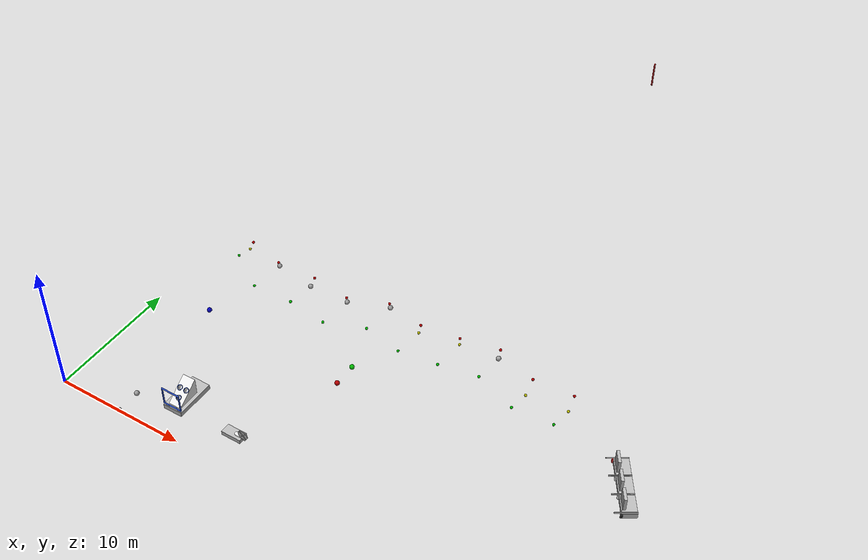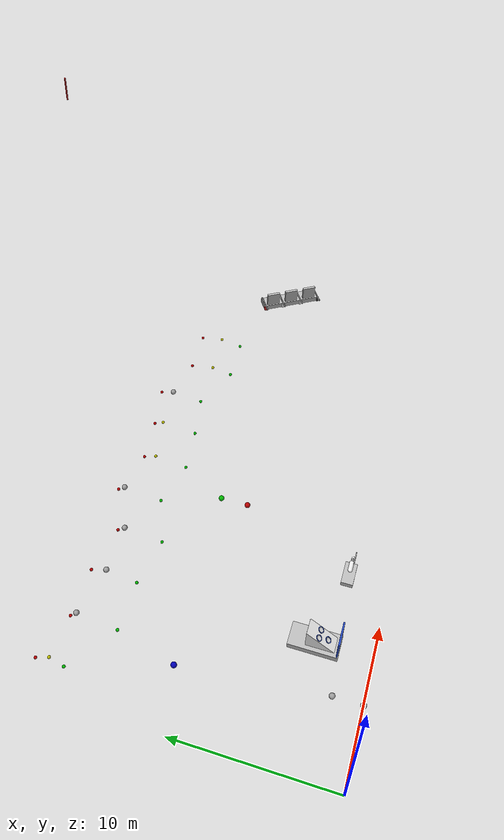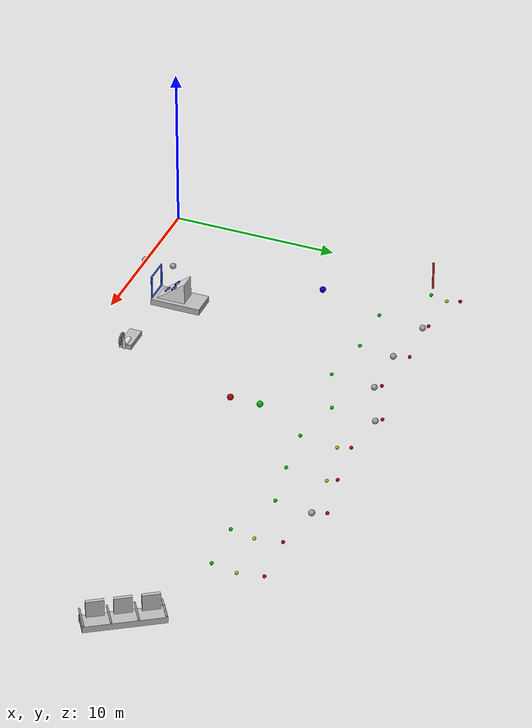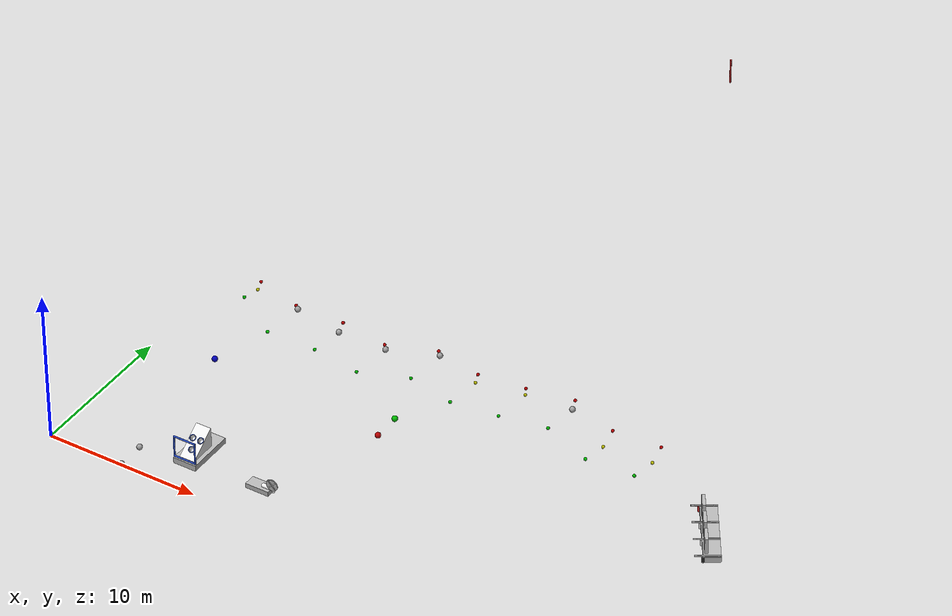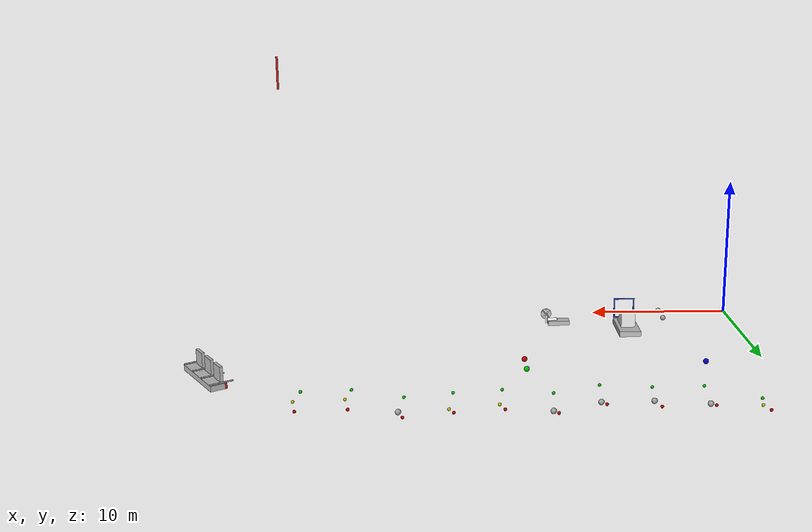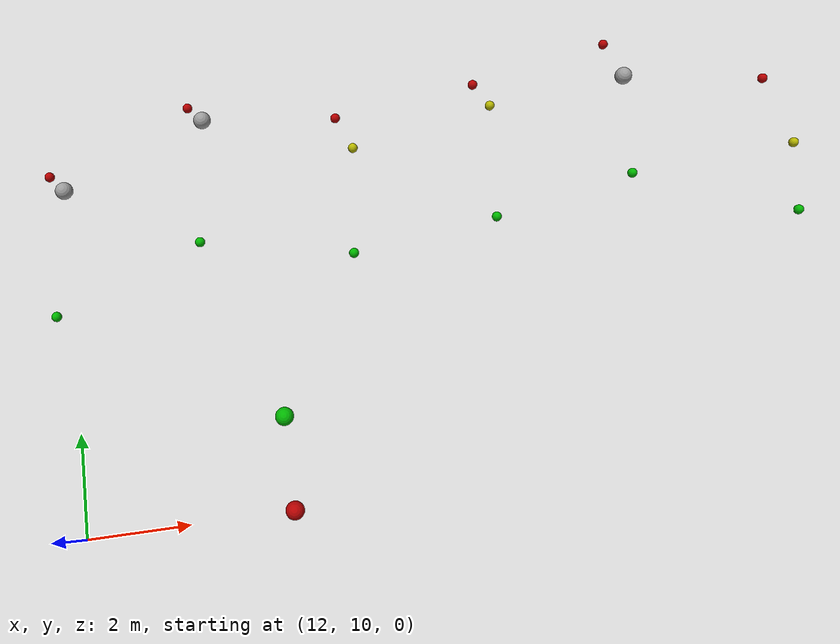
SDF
<sdf version="1.6">
 <world name="default">
  <include><uri>model://sun</uri></include>
  <gravity>0 0 -9.8</gravity>
  <magnetic_field>6e-06 2.3e-05 -4.2e-05</magnetic_field>
  <atmosphere type="adiabatic"/>
  <physics type="ode">
   <max_step_size>0.001</max_step_size>
   <real_time_factor>1</real_time_factor>
   <real_time_update_rate>1000</real_time_update_rate>
  </physics>
  <scene><ambient>0.4 0.4 0.4 1</ambient><background>0.7 0.7 0.7 1</background><shadows>1</shadows></scene>
  <spherical_coordinates>
   <surface_model>EARTH_WGS84</surface_model>
   <latitude_deg>0</latitude_deg>
   <longitude_deg>0</longitude_deg>
   <elevation>0</elevation>
   <heading_deg>0</heading_deg>
  </spherical_coordinates>
  <include><uri>model://task2_model</uri><pose>2 18 0 0 0 -1.57</pose></include>
  <include><uri>model://task3_model</uri><pose>37 10 0 0 0 -1</pose></include>
  <include><uri>model://task4_model</uri><pose>16 10 0 0 0 0</pose></include>
  <include><uri>model://task6_model</uri><pose>8 4 0 1.57 0 0</pose></include>
  <include><uri>model://task7_model</uri><pose>13 2.5 0 1.57 0 1.57</pose></include>
  <include><uri>model://task8_model</uri><pose>5 0 0 0 0 0</pose></include>
 </world>
</sdf>

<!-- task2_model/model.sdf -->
<sdf version='1.6'>
<model name="task2">
 <model name="Small gate buoy (red) #1">
    <pose>-0.730061763372986 0 0 0 0 0</pose>
    <static>1</static>
    <link name="sphere">
      <inertial>
        <mass>1</mass>
        <inertia>
            <ixx>0.06773</ixx>
            <ixy>0</ixy>
            <ixz>0</ixz>
            <iyy>0.06773</iyy>
            <iyz>0</iyz>
            <izz>0.06773</izz>
        </inertia>
        <pose>0 0 0 0 -0 0</pose>
      </inertial>
      <gravity>1</gravity>
      <self_collide>0</self_collide>
      <enable_wind>0</enable_wind>
      <kinematic>0</kinematic>
      <visual name="visual">
        <geometry>
          <sphere>
            <radius>0.1016</radius>
          </sphere>
        </geometry>
        <material>
          <lighting>1</lighting>
          <script>
            <uri>file://media/materials/scripts/gazebo.material</uri>
            <name>Gazebo/Grey</name>
          </script>
          <shader type="pixel">
            <normal_map>__default__</normal_map>
          </shader>
          <ambient>0.3 0.3 0.3 1</ambient>
          <!-- Red color -->
          <diffuse>0.7 0 0 1</diffuse>
          <specular>0.01 0.01 0.01 1</specular>
          <emissive>0 0 0 1</emissive>
        </material>
        <transparency>0</transparency>
        <cast_shadows>1</cast_shadows>
      </visual>
      <collision name="collision">
        <geometry>
          <sphere>
            <radius>0.1016</radius>
          </sphere>
        </geometry>
        <max_contacts>10</max_contacts>
        <surface>
          <friction>
            <ode>
              <mu>1</mu>
              <mu2>1</mu2>
              <fdir1>0 0 0</fdir1>
              <slip1>0</slip1>
              <slip2>0</slip2>
            </ode>
            <torsional>
              <coefficient>1</coefficient>
              <patch_radius>0</patch_radius>
              <surface_radius>0</surface_radius>
              <use_patch_radius>1</use_patch_radius>
              <ode>
                <slip>0</slip>
              </ode>
            </torsional>
          </friction>
          <bounce>
            <restitution_coefficient>0</restitution_coefficient>
            <threshold>1e+06</threshold>
          </bounce>
          <contact>
            <collide_without_contact>0</collide_without_contact>
            <collide_without_contact_bitmask>1</collide_without_contact_bitmask>
            <collide_bitmask>1</collide_bitmask>
            <ode>
              <soft_cfm>0</soft_cfm>
              <soft_erp>0.2</soft_erp>
              <kp>1e+13</kp>
              <kd>1</kd>
              <max_vel>0.01</max_vel>
              <min_depth>0</min_depth>
            </ode>
            <bullet>
              <split_impulse>1</split_impulse>
              <split_impulse_penetration_threshold>-0.01</split_impulse_penetration_threshold>
              <soft_cfm>0</soft_cfm>
              <soft_erp>0.2</soft_erp>
              <kp>1e+13</kp>
              <kd>1</kd>
            </bullet>
          </contact>
        </surface>
      </collision>
    </link>
  </model>
<model name="Small gate buoy (green) #1">
    <pose>1.069938236627014 0 0 0 0 0</pose>
    <static>1</static>
    <link name="sphere">
      <inertial>
        <mass>1</mass>
        <inertia>
            <ixx>0.06773</ixx>
            <ixy>0</ixy>
            <ixz>0</ixz>
            <iyy>0.06773</iyy>
            <iyz>0</iyz>
            <izz>0.06773</izz>
        </inertia>
        <pose>0 0 0 0 -0 0</pose>
      </inertial>
      <gravity>1</gravity>
      <self_collide>0</self_collide>
      <enable_wind>0</enable_wind>
      <kinematic>0</kinematic>
      <visual name="visual">
        <geometry>
          <sphere>
            <radius>0.1016</radius>
          </sphere>
        </geometry>
        <material>
          <lighting>1</lighting>
          <script>
            <uri>file://media/materials/scripts/gazebo.material</uri>
            <name>Gazebo/Grey</name>
          </script>
          <shader type="pixel">
            <normal_map>__default__</normal_map>
          </shader>
          <ambient>0.3 0.3 0.3 1</ambient>
          <!-- Green color -->
          <diffuse>0 0.7 0 1</diffuse>
          <specular>0.01 0.01 0.01 1</specular>
          <emissive>0 0 0 1</emissive>
        </material>
        <transparency>0</transparency>
        <cast_shadows>1</cast_shadows>
      </visual>
      <collision name="collision">
        <geometry>
          <sphere>
            <radius>0.1016</radius>
          </sphere>
        </geometry>
        <max_contacts>10</max_contacts>
        <surface>
          <friction>
            <ode>
              <mu>1</mu>
              <mu2>1</mu2>
              <fdir1>0 0 0</fdir1>
              <slip1>0</slip1>
              <slip2>0</slip2>
            </ode>
            <torsional>
              <coefficient>1</coefficient>
              <patch_radius>0</patch_radius>
              <surface_radius>0</surface_radius>
              <use_patch_radius>1</use_patch_radius>
              <ode>
                <slip>0</slip>
              </ode>
            </torsional>
          </friction>
          <bounce>
            <restitution_coefficient>0</restitution_coefficient>
            <threshold>1e+06</threshold>
          </bounce>
          <contact>
            <collide_without_contact>0</collide_without_contact>
            <collide_without_contact_bitmask>1</collide_without_contact_bitmask>
            <collide_bitmask>1</collide_bitmask>
            <ode>
              <soft_cfm>0</soft_cfm>
              <soft_erp>0.2</soft_erp>
              <kp>1e+13</kp>
              <kd>1</kd>
              <max_vel>0.01</max_vel>
              <min_depth>0</min_depth>
            </ode>
            <bullet>
              <split_impulse>1</split_impulse>
              <split_impulse_penetration_threshold>-0.01</split_impulse_penetration_threshold>
              <soft_cfm>0</soft_cfm>
              <soft_erp>0.2</soft_erp>
              <kp>1e+13</kp>
              <kd>1</kd>
            </bullet>
          </contact>
        </surface>
      </collision>
    </link>
  </model>
<model name="Small gate buoy (yellow) #1">
    <pose>0.011012569928016136 0.26362526975244704 0 0 0 0</pose>
    <static>1</static>
    <link name="sphere">
      <inertial>
        <mass>1</mass>
        <inertia>
          <ixx>0.06773</ixx>
          <ixy>0</ixy>
          <ixz>0</ixz>
          <iyy>0.06773</iyy>
          <iyz>0</iyz>
          <izz>0.06773</izz>
        </inertia>
        <pose>0 0 0 0 -0 0</pose>
      </inertial>
      <gravity>1</gravity>
      <self_collide>0</self_collide>
      <enable_wind>0</enable_wind>
      <kinematic>0</kinematic>
      <visual name="visual">
        <geometry>
          <sphere>
            <radius>0.1016</radius>
          </sphere>
        </geometry>
        <material>
          <lighting>1</lighting>
          <script>
            <name>Gazebo/Grey</name>
            <uri>file://media/materials/scripts/gazebo.material</uri>
          </script>
          <shader type="pixel">
            <normal_map>__default__</normal_map>
          </shader>
          <ambient>0.3 0.3 0.3 1</ambient>
          <!-- Yellow color -->
          <diffuse>0.7 0.7 0 1</diffuse>
          <specular>0.01 0.01 0.01 1</specular>
          <emissive>0 0 0 1</emissive>
        </material>
        <transparency>0</transparency>
        <cast_shadows>1</cast_shadows>
      </visual>
      <collision name="collision">
        <geometry>
          <sphere>
            <radius>0.1016</radius>
          </sphere>
        </geometry>
        <max_contacts>10</max_contacts>
        <surface>
          <friction>
            <ode>
              <mu>1</mu>
              <mu2>1</mu2>
              <fdir1>0 0 0</fdir1>
              <slip1>0</slip1>
              <slip2>0</slip2>
            </ode>
            <torsional>
              <coefficient>1</coefficient>
              <patch_radius>0</patch_radius>
              <surface_radius>0</surface_radius>
              <use_patch_radius>1</use_patch_radius>
              <ode>
                <slip>0</slip>
              </ode>
            </torsional>
          </friction>
          <bounce>
            <restitution_coefficient>0</restitution_coefficient>
            <threshold>1e+06</threshold>
          </bounce>
          <contact>
            <collide_without_contact>0</collide_without_contact>
            <collide_without_contact_bitmask>1</collide_without_contact_bitmask>
            <collide_bitmask>1</collide_bitmask>
            <ode>
              <soft_cfm>0</soft_cfm>
              <soft_erp>0.2</soft_erp>
              <kp>1e+13</kp>
              <kd>1</kd>
              <max_vel>0.01</max_vel>
              <min_depth>0</min_depth>
            </ode>
            <bullet>
              <split_impulse>1</split_impulse>
              <split_impulse_penetration_threshold>-0.01</split_impulse_penetration_threshold>
              <soft_cfm>0</soft_cfm>
              <soft_erp>0.2</soft_erp>
              <kp>1e+13</kp>
              <kd>1</kd>
            </bullet>
          </contact>
        </surface>
      </collision>
    </link>
  </model>
<model name="Small gate buoy (red) #2">
    <pose>0.1072216156817205 3.074549545443854 0 0 0 0</pose>
    <static>1</static>
    <link name="sphere">
      <inertial>
        <mass>1</mass>
        <inertia>
            <ixx>0.06773</ixx>
            <ixy>0</ixy>
            <ixz>0</ixz>
            <iyy>0.06773</iyy>
            <iyz>0</iyz>
            <izz>0.06773</izz>
        </inertia>
        <pose>0 0 0 0 -0 0</pose>
      </inertial>
      <gravity>1</gravity>
      <self_collide>0</self_collide>
      <enable_wind>0</enable_wind>
      <kinematic>0</kinematic>
      <visual name="visual">
        <geometry>
          <sphere>
            <radius>0.1016</radius>
          </sphere>
        </geometry>
        <material>
          <lighting>1</lighting>
          <script>
            <uri>file://media/materials/scripts/gazebo.material</uri>
            <name>Gazebo/Grey</name>
          </script>
          <shader type="pixel">
            <normal_map>__default__</normal_map>
          </shader>
          <ambient>0.3 0.3 0.3 1</ambient>
          <!-- Red color -->
          <diffuse>0.7 0 0 1</diffuse>
          <specular>0.01 0.01 0.01 1</specular>
          <emissive>0 0 0 1</emissive>
        </material>
        <transparency>0</transparency>
        <cast_shadows>1</cast_shadows>
      </visual>
      <collision name="collision">
        <geometry>
          <sphere>
            <radius>0.1016</radius>
          </sphere>
        </geometry>
        <max_contacts>10</max_contacts>
        <surface>
          <friction>
            <ode>
              <mu>1</mu>
              <mu2>1</mu2>
              <fdir1>0 0 0</fdir1>
              <slip1>0</slip1>
              <slip2>0</slip2>
            </ode>
            <torsional>
              <coefficient>1</coefficient>
              <patch_radius>0</patch_radius>
              <surface_radius>0</surface_radius>
              <use_patch_radius>1</use_patch_radius>
              <ode>
                <slip>0</slip>
              </ode>
            </torsional>
          </friction>
          <bounce>
            <restitution_coefficient>0</restitution_coefficient>
            <threshold>1e+06</threshold>
          </bounce>
          <contact>
            <collide_without_contact>0</collide_without_contact>
            <collide_without_contact_bitmask>1</collide_without_contact_bitmask>
            <collide_bitmask>1</collide_bitmask>
            <ode>
              <soft_cfm>0</soft_cfm>
              <soft_erp>0.2</soft_erp>
              <kp>1e+13</kp>
              <kd>1</kd>
              <max_vel>0.01</max_vel>
              <min_depth>0</min_depth>
            </ode>
            <bullet>
              <split_impulse>1</split_impulse>
              <split_impulse_penetration_threshold>-0.01</split_impulse_penetration_threshold>
              <soft_cfm>0</soft_cfm>
              <soft_erp>0.2</soft_erp>
              <kp>1e+13</kp>
              <kd>1</kd>
            </bullet>
          </contact>
        </surface>
      </collision>
    </link>
  </model>
<model name="Small gate buoy (green) #2">
    <pose>3.15522161568 3.074549545443854 0 0 0 0</pose>
    <static>1</static>
    <link name="sphere">
      <inertial>
        <mass>1</mass>
        <inertia>
            <ixx>0.06773</ixx>
            <ixy>0</ixy>
            <ixz>0</ixz>
            <iyy>0.06773</iyy>
            <iyz>0</iyz>
            <izz>0.06773</izz>
        </inertia>
        <pose>0 0 0 0 -0 0</pose>
      </inertial>
      <gravity>1</gravity>
      <self_collide>0</self_collide>
      <enable_wind>0</enable_wind>
      <kinematic>0</kinematic>
      <visual name="visual">
        <geometry>
          <sphere>
            <radius>0.1016</radius>
          </sphere>
        </geometry>
        <material>
          <lighting>1</lighting>
          <script>
            <uri>file://media/materials/scripts/gazebo.material</uri>
            <name>Gazebo/Grey</name>
          </script>
          <shader type="pixel">
            <normal_map>__default__</normal_map>
          </shader>
          <ambient>0.3 0.3 0.3 1</ambient>
          <!-- Green color -->
          <diffuse>0 0.7 0 1</diffuse>
          <specular>0.01 0.01 0.01 1</specular>
          <emissive>0 0 0 1</emissive>
        </material>
        <transparency>0</transparency>
        <cast_shadows>1</cast_shadows>
      </visual>
      <collision name="collision">
        <geometry>
          <sphere>
            <radius>0.1016</radius>
          </sphere>
        </geometry>
        <max_contacts>10</max_contacts>
        <surface>
          <friction>
            <ode>
              <mu>1</mu>
              <mu2>1</mu2>
              <fdir1>0 0 0</fdir1>
              <slip1>0</slip1>
              <slip2>0</slip2>
            </ode>
            <torsional>
              <coefficient>1</coefficient>
              <patch_radius>0</patch_radius>
              <surface_radius>0</surface_radius>
              <use_patch_radius>1</use_patch_radius>
              <ode>
                <slip>0</slip>
              </ode>
            </torsional>
          </friction>
          <bounce>
            <restitution_coefficient>0</restitution_coefficient>
            <threshold>1e+06</threshold>
          </bounce>
          <contact>
            <collide_without_contact>0</collide_without_contact>
            <collide_without_contact_bitmask>1</collide_without_contact_bitmask>
            <collide_bitmask>1</collide_bitmask>
            <ode>
              <soft_cfm>0</soft_cfm>
              <soft_erp>0.2</soft_erp>
              <kp>1e+13</kp>
              <kd>1</kd>
              <max_vel>0.01</max_vel>
              <min_depth>0</min_depth>
            </ode>
            <bullet>
              <split_impulse>1</split_impulse>
              <split_impulse_penetration_threshold>-0.01</split_impulse_penetration_threshold>
              <soft_cfm>0</soft_cfm>
              <soft_erp>0.2</soft_erp>
              <kp>1e+13</kp>
              <kd>1</kd>
            </bullet>
          </contact>
        </surface>
      </collision>
    </link>
  </model>
<model name="Gate buoy (black) #2">
    <pose>0.3627652627230137 3.3600615542844396 0 0 0 0</pose>
    <static>1</static>
    <link name="sphere">
      <inertial>
        <mass>1</mass>
        <inertia>
          <ixx>0.0135645</ixx>
          <ixy>0</ixy>
          <ixz>0</ixz>
          <iyy>0.0135645</iyy>
          <iyz>0</iyz>
          <izz>0.0135645</izz>
        </inertia>
        <pose>0 0 0 0 -0 0</pose>
      </inertial>
      <gravity>1</gravity>
      <self_collide>0</self_collide>
      <enable_wind>0</enable_wind>
      <kinematic>0</kinematic>
      <visual name="visual">
        <geometry>
          <sphere>
            <radius>0.18415</radius>
          </sphere>
        </geometry>
        <material>
          <lighting>1</lighting>
          <script>
            <uri>file://media/materials/scripts/gazebo.material</uri>
            <name>Gazebo/Grey</name>
          </script>
          <shader type="pixel">
            <normal_map>__default__</normal_map>
          </shader>
          <ambient>0.3 0.3 0.3 1</ambient>
          <!-- Black color -->
          <diffuse>0 0 0 1</diffuse>
          <specular>0.01 0.01 0.01 1</specular>
          <emissive>0 0 0 1</emissive>
        </material>
        <transparency>0</transparency>
        <cast_shadows>1</cast_shadows>
      </visual>
      <collision name="collision">
        <geometry>
          <sphere>
            <radius>0.18415</radius>
          </sphere>
        </geometry>
        <max_contacts>10</max_contacts>
        <surface>
          <friction>
            <ode>
              <mu>1</mu>
              <mu2>1</mu2>
              <fdir1>0 0 0</fdir1>
              <slip1>0</slip1>
              <slip2>0</slip2>
            </ode>
            <torsional>
              <coefficient>1</coefficient>
              <patch_radius>0</patch_radius>
              <surface_radius>0</surface_radius>
              <use_patch_radius>1</use_patch_radius>
              <ode>
                <slip>0</slip>
              </ode>
            </torsional>
          </friction>
          <bounce>
            <restitution_coefficient>0</restitution_coefficient>
            <threshold>1e+06</threshold>
          </bounce>
          <contact>
            <collide_without_contact>0</collide_without_contact>
            <collide_without_contact_bitmask>1</collide_without_contact_bitmask>
            <collide_bitmask>1</collide_bitmask>
            <ode>
              <soft_cfm>0</soft_cfm>
              <soft_erp>0.2</soft_erp>
              <kp>1e+13</kp>
              <kd>1</kd>
              <max_vel>0.01</max_vel>
              <min_depth>0</min_depth>
            </ode>
            <bullet>
              <split_impulse>1</split_impulse>
              <split_impulse_penetration_threshold>-0.01</split_impulse_penetration_threshold>
              <soft_cfm>0</soft_cfm>
              <soft_erp>0.2</soft_erp>
              <kp>1e+13</kp>
              <kd>1</kd>
            </bullet>
          </contact>
        </surface>
      </collision>
    </link>
  </model>
<model name="Small gate buoy (red) #3">
    <pose>0.04811401423226713 6.380495701676587 0 0 0 0</pose>
    <static>1</static>
    <link name="sphere">
      <inertial>
        <mass>1</mass>
        <inertia>
            <ixx>0.06773</ixx>
            <ixy>0</ixy>
            <ixz>0</ixz>
            <iyy>0.06773</iyy>
            <iyz>0</iyz>
            <izz>0.06773</izz>
        </inertia>
        <pose>0 0 0 0 -0 0</pose>
      </inertial>
      <gravity>1</gravity>
      <self_collide>0</self_collide>
      <enable_wind>0</enable_wind>
      <kinematic>0</kinematic>
      <visual name="visual">
        <geometry>
          <sphere>
            <radius>0.1016</radius>
          </sphere>
        </geometry>
        <material>
          <lighting>1</lighting>
          <script>
            <uri>file://media/materials/scripts/gazebo.material</uri>
            <name>Gazebo/Grey</name>
          </script>
          <shader type="pixel">
            <normal_map>__default__</normal_map>
          </shader>
          <ambient>0.3 0.3 0.3 1</ambient>
          <!-- Red color -->
          <diffuse>0.7 0 0 1</diffuse>
          <specular>0.01 0.01 0.01 1</specular>
          <emissive>0 0 0 1</emissive>
        </material>
        <transparency>0</transparency>
        <cast_shadows>1</cast_shadows>
      </visual>
      <collision name="collision">
        <geometry>
          <sphere>
            <radius>0.1016</radius>
          </sphere>
        </geometry>
        <max_contacts>10</max_contacts>
        <surface>
          <friction>
            <ode>
              <mu>1</mu>
              <mu2>1</mu2>
              <fdir1>0 0 0</fdir1>
              <slip1>0</slip1>
              <slip2>0</slip2>
            </ode>
            <torsional>
              <coefficient>1</coefficient>
              <patch_radius>0</patch_radius>
              <surface_radius>0</surface_radius>
              <use_patch_radius>1</use_patch_radius>
              <ode>
                <slip>0</slip>
              </ode>
            </torsional>
          </friction>
          <bounce>
            <restitution_coefficient>0</restitution_coefficient>
            <threshold>1e+06</threshold>
          </bounce>
          <contact>
            <collide_without_contact>0</collide_without_contact>
            <collide_without_contact_bitmask>1</collide_without_contact_bitmask>
            <collide_bitmask>1</collide_bitmask>
            <ode>
              <soft_cfm>0</soft_cfm>
              <soft_erp>0.2</soft_erp>
              <kp>1e+13</kp>
              <kd>1</kd>
              <max_vel>0.01</max_vel>
              <min_depth>0</min_depth>
            </ode>
            <bullet>
              <split_impulse>1</split_impulse>
              <split_impulse_penetration_threshold>-0.01</split_impulse_penetration_threshold>
              <soft_cfm>0</soft_cfm>
              <soft_erp>0.2</soft_erp>
              <kp>1e+13</kp>
              <kd>1</kd>
            </bullet>
          </contact>
        </surface>
      </collision>
    </link>
  </model>
<model name="Small gate buoy (green) #3">
    <pose>3.09611 6.380495701676587 0 0 0 0</pose>
    <static>1</static>
    <link name="sphere">
      <inertial>
        <mass>1</mass>
        <inertia>
            <ixx>0.06773</ixx>
            <ixy>0</ixy>
            <ixz>0</ixz>
            <iyy>0.06773</iyy>
            <iyz>0</iyz>
            <izz>0.06773</izz>
        </inertia>
        <pose>0 0 0 0 -0 0</pose>
      </inertial>
      <gravity>1</gravity>
      <self_collide>0</self_collide>
      <enable_wind>0</enable_wind>
      <kinematic>0</kinematic>
      <visual name="visual">
        <geometry>
          <sphere>
            <radius>0.1016</radius>
          </sphere>
        </geometry>
        <material>
          <lighting>1</lighting>
          <script>
            <uri>file://media/materials/scripts/gazebo.material</uri>
            <name>Gazebo/Grey</name>
          </script>
          <shader type="pixel">
            <normal_map>__default__</normal_map>
          </shader>
          <ambient>0.3 0.3 0.3 1</ambient>
          <!-- Green color -->
          <diffuse>0 0.7 0 1</diffuse>
          <specular>0.01 0.01 0.01 1</specular>
          <emissive>0 0 0 1</emissive>
        </material>
        <transparency>0</transparency>
        <cast_shadows>1</cast_shadows>
      </visual>
      <collision name="collision">
        <geometry>
          <sphere>
            <radius>0.1016</radius>
          </sphere>
        </geometry>
        <max_contacts>10</max_contacts>
        <surface>
          <friction>
            <ode>
              <mu>1</mu>
              <mu2>1</mu2>
              <fdir1>0 0 0</fdir1>
              <slip1>0</slip1>
              <slip2>0</slip2>
            </ode>
            <torsional>
              <coefficient>1</coefficient>
              <patch_radius>0</patch_radius>
              <surface_radius>0</surface_radius>
              <use_patch_radius>1</use_patch_radius>
              <ode>
                <slip>0</slip>
              </ode>
            </torsional>
          </friction>
          <bounce>
            <restitution_coefficient>0</restitution_coefficient>
            <threshold>1e+06</threshold>
          </bounce>
          <contact>
            <collide_without_contact>0</collide_without_contact>
            <collide_without_contact_bitmask>1</collide_without_contact_bitmask>
            <collide_bitmask>1</collide_bitmask>
            <ode>
              <soft_cfm>0</soft_cfm>
              <soft_erp>0.2</soft_erp>
              <kp>1e+13</kp>
              <kd>1</kd>
              <max_vel>0.01</max_vel>
              <min_depth>0</min_depth>
            </ode>
            <bullet>
              <split_impulse>1</split_impulse>
              <split_impulse_penetration_threshold>-0.01</split_impulse_penetration_threshold>
              <soft_cfm>0</soft_cfm>
              <soft_erp>0.2</soft_erp>
              <kp>1e+13</kp>
              <kd>1</kd>
            </bullet>
          </contact>
        </surface>
      </collision>
    </link>
  </model>
<model name="Gate buoy (black) #3">
    <pose>0.9390683070982704 6.666007710517173 0 0 0 0</pose>
    <static>1</static>
    <link name="sphere">
      <inertial>
        <mass>1</mass>
        <inertia>
          <ixx>0.0135645</ixx>
          <ixy>0</ixy>
          <ixz>0</ixz>
          <iyy>0.0135645</iyy>
          <iyz>0</iyz>
          <izz>0.0135645</izz>
        </inertia>
        <pose>0 0 0 0 -0 0</pose>
      </inertial>
      <gravity>1</gravity>
      <self_collide>0</self_collide>
      <enable_wind>0</enable_wind>
      <kinematic>0</kinematic>
      <visual name="visual">
        <geometry>
          <sphere>
            <radius>0.18415</radius>
          </sphere>
        </geometry>
        <material>
          <lighting>1</lighting>
          <script>
            <uri>file://media/materials/scripts/gazebo.material</uri>
            <name>Gazebo/Grey</name>
          </script>
          <shader type="pixel">
            <normal_map>__default__</normal_map>
          </shader>
          <ambient>0.3 0.3 0.3 1</ambient>
          <!-- Black color -->
          <diffuse>0 0 0 1</diffuse>
          <specular>0.01 0.01 0.01 1</specular>
          <emissive>0 0 0 1</emissive>
        </material>
        <transparency>0</transparency>
        <cast_shadows>1</cast_shadows>
      </visual>
      <collision name="collision">
        <geometry>
          <sphere>
            <radius>0.18415</radius>
          </sphere>
        </geometry>
        <max_contacts>10</max_contacts>
        <surface>
          <friction>
            <ode>
              <mu>1</mu>
              <mu2>1</mu2>
              <fdir1>0 0 0</fdir1>
              <slip1>0</slip1>
              <slip2>0</slip2>
            </ode>
            <torsional>
              <coefficient>1</coefficient>
              <patch_radius>0</patch_radius>
              <surface_radius>0</surface_radius>
              <use_patch_radius>1</use_patch_radius>
              <ode>
                <slip>0</slip>
              </ode>
            </torsional>
          </friction>
          <bounce>
            <restitution_coefficient>0</restitution_coefficient>
            <threshold>1e+06</threshold>
          </bounce>
          <contact>
            <collide_without_contact>0</collide_without_contact>
            <collide_without_contact_bitmask>1</collide_without_contact_bitmask>
            <collide_bitmask>1</collide_bitmask>
            <ode>
              <soft_cfm>0</soft_cfm>
              <soft_erp>0.2</soft_erp>
              <kp>1e+13</kp>
              <kd>1</kd>
              <max_vel>0.01</max_vel>
              <min_depth>0</min_depth>
            </ode>
            <bullet>
              <split_impulse>1</split_impulse>
              <split_impulse_penetration_threshold>-0.01</split_impulse_penetration_threshold>
              <soft_cfm>0</soft_cfm>
              <soft_erp>0.2</soft_erp>
              <kp>1e+13</kp>
              <kd>1</kd>
            </bullet>
          </contact>
        </surface>
      </collision>
    </link>
  </model>
<model name="Small gate buoy (red) #4">
    <pose>0.5256771999983207 9.629806590142618 0 0 0 0</pose>
    <static>1</static>
    <link name="sphere">
      <inertial>
        <mass>1</mass>
        <inertia>
            <ixx>0.06773</ixx>
            <ixy>0</ixy>
            <ixz>0</ixz>
            <iyy>0.06773</iyy>
            <iyz>0</iyz>
            <izz>0.06773</izz>
        </inertia>
        <pose>0 0 0 0 -0 0</pose>
      </inertial>
      <gravity>1</gravity>
      <self_collide>0</self_collide>
      <enable_wind>0</enable_wind>
      <kinematic>0</kinematic>
      <visual name="visual">
        <geometry>
          <sphere>
            <radius>0.1016</radius>
          </sphere>
        </geometry>
        <material>
          <lighting>1</lighting>
          <script>
            <uri>file://media/materials/scripts/gazebo.material</uri>
            <name>Gazebo/Grey</name>
          </script>
          <shader type="pixel">
            <normal_map>__default__</normal_map>
          </shader>
          <ambient>0.3 0.3 0.3 1</ambient>
          <!-- Red color -->
          <diffuse>0.7 0 0 1</diffuse>
          <specular>0.01 0.01 0.01 1</specular>
          <emissive>0 0 0 1</emissive>
        </material>
        <transparency>0</transparency>
        <cast_shadows>1</cast_shadows>
      </visual>
      <collision name="collision">
        <geometry>
          <sphere>
            <radius>0.1016</radius>
          </sphere>
        </geometry>
        <max_contacts>10</max_contacts>
        <surface>
          <friction>
            <ode>
              <mu>1</mu>
              <mu2>1</mu2>
              <fdir1>0 0 0</fdir1>
              <slip1>0</slip1>
              <slip2>0</slip2>
            </ode>
            <torsional>
              <coefficient>1</coefficient>
              <patch_radius>0</patch_radius>
              <surface_radius>0</surface_radius>
              <use_patch_radius>1</use_patch_radius>
              <ode>
                <slip>0</slip>
              </ode>
            </torsional>
          </friction>
          <bounce>
            <restitution_coefficient>0</restitution_coefficient>
            <threshold>1e+06</threshold>
          </bounce>
          <contact>
            <collide_without_contact>0</collide_without_contact>
            <collide_without_contact_bitmask>1</collide_without_contact_bitmask>
            <collide_bitmask>1</collide_bitmask>
            <ode>
              <soft_cfm>0</soft_cfm>
              <soft_erp>0.2</soft_erp>
              <kp>1e+13</kp>
              <kd>1</kd>
              <max_vel>0.01</max_vel>
              <min_depth>0</min_depth>
            </ode>
            <bullet>
              <split_impulse>1</split_impulse>
              <split_impulse_penetration_threshold>-0.01</split_impulse_penetration_threshold>
              <soft_cfm>0</soft_cfm>
              <soft_erp>0.2</soft_erp>
              <kp>1e+13</kp>
              <kd>1</kd>
            </bullet>
          </contact>
        </surface>
      </collision>
    </link>
  </model>
<model name="Small gate buoy (green) #4">
    <pose>3.573677 9.629806590142618 0 0 0 0</pose>
    <static>1</static>
    <link name="sphere">
      <inertial>
        <mass>1</mass>
        <inertia>
            <ixx>0.06773</ixx>
            <ixy>0</ixy>
            <ixz>0</ixz>
            <iyy>0.06773</iyy>
            <iyz>0</iyz>
            <izz>0.06773</izz>
        </inertia>
        <pose>0 0 0 0 -0 0</pose>
      </inertial>
      <gravity>1</gravity>
      <self_collide>0</self_collide>
      <enable_wind>0</enable_wind>
      <kinematic>0</kinematic>
      <visual name="visual">
        <geometry>
          <sphere>
            <radius>0.1016</radius>
          </sphere>
        </geometry>
        <material>
          <lighting>1</lighting>
          <script>
            <uri>file://media/materials/scripts/gazebo.material</uri>
            <name>Gazebo/Grey</name>
          </script>
          <shader type="pixel">
            <normal_map>__default__</normal_map>
          </shader>
          <ambient>0.3 0.3 0.3 1</ambient>
          <!-- Green color -->
          <diffuse>0 0.7 0 1</diffuse>
          <specular>0.01 0.01 0.01 1</specular>
          <emissive>0 0 0 1</emissive>
        </material>
        <transparency>0</transparency>
        <cast_shadows>1</cast_shadows>
      </visual>
      <collision name="collision">
        <geometry>
          <sphere>
            <radius>0.1016</radius>
          </sphere>
        </geometry>
        <max_contacts>10</max_contacts>
        <surface>
          <friction>
            <ode>
              <mu>1</mu>
              <mu2>1</mu2>
              <fdir1>0 0 0</fdir1>
              <slip1>0</slip1>
              <slip2>0</slip2>
            </ode>
            <torsional>
              <coefficient>1</coefficient>
              <patch_radius>0</patch_radius>
              <surface_radius>0</surface_radius>
              <use_patch_radius>1</use_patch_radius>
              <ode>
                <slip>0</slip>
              </ode>
            </torsional>
          </friction>
          <bounce>
            <restitution_coefficient>0</restitution_coefficient>
            <threshold>1e+06</threshold>
          </bounce>
          <contact>
            <collide_without_contact>0</collide_without_contact>
            <collide_without_contact_bitmask>1</collide_without_contact_bitmask>
            <collide_bitmask>1</collide_bitmask>
            <ode>
              <soft_cfm>0</soft_cfm>
              <soft_erp>0.2</soft_erp>
              <kp>1e+13</kp>
              <kd>1</kd>
              <max_vel>0.01</max_vel>
              <min_depth>0</min_depth>
            </ode>
            <bullet>
              <split_impulse>1</split_impulse>
              <split_impulse_penetration_threshold>-0.01</split_impulse_penetration_threshold>
              <soft_cfm>0</soft_cfm>
              <soft_erp>0.2</soft_erp>
              <kp>1e+13</kp>
              <kd>1</kd>
            </bullet>
          </contact>
        </surface>
      </collision>
    </link>
  </model>
<model name="Gate buoy (black) #4">
    <pose>0.8734767325358259 9.915318598983204 0 0 0 0</pose>
    <static>1</static>
    <link name="sphere">
      <inertial>
        <mass>1</mass>
        <inertia>
          <ixx>0.0135645</ixx>
          <ixy>0</ixy>
          <ixz>0</ixz>
          <iyy>0.0135645</iyy>
          <iyz>0</iyz>
          <izz>0.0135645</izz>
        </inertia>
        <pose>0 0 0 0 -0 0</pose>
      </inertial>
      <gravity>1</gravity>
      <self_collide>0</self_collide>
      <enable_wind>0</enable_wind>
      <kinematic>0</kinematic>
      <visual name="visual">
        <geometry>
          <sphere>
            <radius>0.18415</radius>
          </sphere>
        </geometry>
        <material>
          <lighting>1</lighting>
          <script>
            <uri>file://media/materials/scripts/gazebo.material</uri>
            <name>Gazebo/Grey</name>
          </script>
          <shader type="pixel">
            <normal_map>__default__</normal_map>
          </shader>
          <ambient>0.3 0.3 0.3 1</ambient>
          <!-- Black color -->
          <diffuse>0 0 0 1</diffuse>
          <specular>0.01 0.01 0.01 1</specular>
          <emissive>0 0 0 1</emissive>
        </material>
        <transparency>0</transparency>
        <cast_shadows>1</cast_shadows>
      </visual>
      <collision name="collision">
        <geometry>
          <sphere>
            <radius>0.18415</radius>
          </sphere>
        </geometry>
        <max_contacts>10</max_contacts>
        <surface>
          <friction>
            <ode>
              <mu>1</mu>
              <mu2>1</mu2>
              <fdir1>0 0 0</fdir1>
              <slip1>0</slip1>
              <slip2>0</slip2>
            </ode>
            <torsional>
              <coefficient>1</coefficient>
              <patch_radius>0</patch_radius>
              <surface_radius>0</surface_radius>
              <use_patch_radius>1</use_patch_radius>
              <ode>
                <slip>0</slip>
              </ode>
            </torsional>
          </friction>
          <bounce>
            <restitution_coefficient>0</restitution_coefficient>
            <threshold>1e+06</threshold>
          </bounce>
          <contact>
            <collide_without_contact>0</collide_without_contact>
            <collide_without_contact_bitmask>1</collide_without_contact_bitmask>
            <collide_bitmask>1</collide_bitmask>
            <ode>
              <soft_cfm>0</soft_cfm>
              <soft_erp>0.2</soft_erp>
              <kp>1e+13</kp>
              <kd>1</kd>
              <max_vel>0.01</max_vel>
              <min_depth>0</min_depth>
            </ode>
            <bullet>
              <split_impulse>1</split_impulse>
              <split_impulse_penetration_threshold>-0.01</split_impulse_penetration_threshold>
              <soft_cfm>0</soft_cfm>
              <soft_erp>0.2</soft_erp>
              <kp>1e+13</kp>
              <kd>1</kd>
            </bullet>
          </contact>
        </surface>
      </collision>
    </link>
  </model>
<model name="Small gate buoy (red) #5">
    <pose>-0.6572970145109478 12.65723065527346 0 0 0 0</pose>
    <static>1</static>
    <link name="sphere">
      <inertial>
        <mass>1</mass>
        <inertia>
            <ixx>0.06773</ixx>
            <ixy>0</ixy>
            <ixz>0</ixz>
            <iyy>0.06773</iyy>
            <iyz>0</iyz>
            <izz>0.06773</izz>
        </inertia>
        <pose>0 0 0 0 -0 0</pose>
      </inertial>
      <gravity>1</gravity>
      <self_collide>0</self_collide>
      <enable_wind>0</enable_wind>
      <kinematic>0</kinematic>
      <visual name="visual">
        <geometry>
          <sphere>
            <radius>0.1016</radius>
          </sphere>
        </geometry>
        <material>
          <lighting>1</lighting>
          <script>
            <uri>file://media/materials/scripts/gazebo.material</uri>
            <name>Gazebo/Grey</name>
          </script>
          <shader type="pixel">
            <normal_map>__default__</normal_map>
          </shader>
          <ambient>0.3 0.3 0.3 1</ambient>
          <!-- Red color -->
          <diffuse>0.7 0 0 1</diffuse>
          <specular>0.01 0.01 0.01 1</specular>
          <emissive>0 0 0 1</emissive>
        </material>
        <transparency>0</transparency>
        <cast_shadows>1</cast_shadows>
      </visual>
      <collision name="collision">
        <geometry>
          <sphere>
            <radius>0.1016</radius>
          </sphere>
        </geometry>
        <max_contacts>10</max_contacts>
        <surface>
          <friction>
            <ode>
              <mu>1</mu>
              <mu2>1</mu2>
              <fdir1>0 0 0</fdir1>
              <slip1>0</slip1>
              <slip2>0</slip2>
            </ode>
            <torsional>
              <coefficient>1</coefficient>
              <patch_radius>0</patch_radius>
              <surface_radius>0</surface_radius>
              <use_patch_radius>1</use_patch_radius>
              <ode>
                <slip>0</slip>
              </ode>
            </torsional>
          </friction>
          <bounce>
            <restitution_coefficient>0</restitution_coefficient>
            <threshold>1e+06</threshold>
          </bounce>
          <contact>
            <collide_without_contact>0</collide_without_contact>
            <collide_without_contact_bitmask>1</collide_without_contact_bitmask>
            <collide_bitmask>1</collide_bitmask>
            <ode>
              <soft_cfm>0</soft_cfm>
              <soft_erp>0.2</soft_erp>
              <kp>1e+13</kp>
              <kd>1</kd>
              <max_vel>0.01</max_vel>
              <min_depth>0</min_depth>
            </ode>
            <bullet>
              <split_impulse>1</split_impulse>
              <split_impulse_penetration_threshold>-0.01</split_impulse_penetration_threshold>
              <soft_cfm>0</soft_cfm>
              <soft_erp>0.2</soft_erp>
              <kp>1e+13</kp>
              <kd>1</kd>
            </bullet>
          </contact>
        </surface>
      </collision>
    </link>
  </model>
<model name="Small gate buoy (green) #5">
    <pose>2.39070 12.65723065527346 0 0 0 0</pose>
    <static>1</static>
    <link name="sphere">
      <inertial>
        <mass>1</mass>
        <inertia>
            <ixx>0.06773</ixx>
            <ixy>0</ixy>
            <ixz>0</ixz>
            <iyy>0.06773</iyy>
            <iyz>0</iyz>
            <izz>0.06773</izz>
        </inertia>
        <pose>0 0 0 0 -0 0</pose>
      </inertial>
      <gravity>1</gravity>
      <self_collide>0</self_collide>
      <enable_wind>0</enable_wind>
      <kinematic>0</kinematic>
      <visual name="visual">
        <geometry>
          <sphere>
            <radius>0.1016</radius>
          </sphere>
        </geometry>
        <material>
          <lighting>1</lighting>
          <script>
            <uri>file://media/materials/scripts/gazebo.material</uri>
            <name>Gazebo/Grey</name>
          </script>
          <shader type="pixel">
            <normal_map>__default__</normal_map>
          </shader>
          <ambient>0.3 0.3 0.3 1</ambient>
          <!-- Green color -->
          <diffuse>0 0.7 0 1</diffuse>
          <specular>0.01 0.01 0.01 1</specular>
          <emissive>0 0 0 1</emissive>
        </material>
        <transparency>0</transparency>
        <cast_shadows>1</cast_shadows>
      </visual>
      <collision name="collision">
        <geometry>
          <sphere>
            <radius>0.1016</radius>
          </sphere>
        </geometry>
        <max_contacts>10</max_contacts>
        <surface>
          <friction>
            <ode>
              <mu>1</mu>
              <mu2>1</mu2>
              <fdir1>0 0 0</fdir1>
              <slip1>0</slip1>
              <slip2>0</slip2>
            </ode>
            <torsional>
              <coefficient>1</coefficient>
              <patch_radius>0</patch_radius>
              <surface_radius>0</surface_radius>
              <use_patch_radius>1</use_patch_radius>
              <ode>
                <slip>0</slip>
              </ode>
            </torsional>
          </friction>
          <bounce>
            <restitution_coefficient>0</restitution_coefficient>
            <threshold>1e+06</threshold>
          </bounce>
          <contact>
            <collide_without_contact>0</collide_without_contact>
            <collide_without_contact_bitmask>1</collide_without_contact_bitmask>
            <collide_bitmask>1</collide_bitmask>
            <ode>
              <soft_cfm>0</soft_cfm>
              <soft_erp>0.2</soft_erp>
              <kp>1e+13</kp>
              <kd>1</kd>
              <max_vel>0.01</max_vel>
              <min_depth>0</min_depth>
            </ode>
            <bullet>
              <split_impulse>1</split_impulse>
              <split_impulse_penetration_threshold>-0.01</split_impulse_penetration_threshold>
              <soft_cfm>0</soft_cfm>
              <soft_erp>0.2</soft_erp>
              <kp>1e+13</kp>
              <kd>1</kd>
            </bullet>
          </contact>
        </surface>
      </collision>
    </link>
  </model>
<model name="Gate buoy (black) #5">
    <pose>-0.33663122403114837 12.942742664114046 0 0 0 0</pose>
    <static>1</static>
    <link name="sphere">
      <inertial>
        <mass>1</mass>
        <inertia>
          <ixx>0.0135645</ixx>
          <ixy>0</ixy>
          <ixz>0</ixz>
          <iyy>0.0135645</iyy>
          <iyz>0</iyz>
          <izz>0.0135645</izz>
        </inertia>
        <pose>0 0 0 0 -0 0</pose>
      </inertial>
      <gravity>1</gravity>
      <self_collide>0</self_collide>
      <enable_wind>0</enable_wind>
      <kinematic>0</kinematic>
      <visual name="visual">
        <geometry>
          <sphere>
            <radius>0.18415</radius>
          </sphere>
        </geometry>
        <material>
          <lighting>1</lighting>
          <script>
            <uri>file://media/materials/scripts/gazebo.material</uri>
            <name>Gazebo/Grey</name>
          </script>
          <shader type="pixel">
            <normal_map>__default__</normal_map>
          </shader>
          <ambient>0.3 0.3 0.3 1</ambient>
          <!-- Black color -->
          <diffuse>0 0 0 1</diffuse>
          <specular>0.01 0.01 0.01 1</specular>
          <emissive>0 0 0 1</emissive>
        </material>
        <transparency>0</transparency>
        <cast_shadows>1</cast_shadows>
      </visual>
      <collision name="collision">
        <geometry>
          <sphere>
            <radius>0.18415</radius>
          </sphere>
        </geometry>
        <max_contacts>10</max_contacts>
        <surface>
          <friction>
            <ode>
              <mu>1</mu>
              <mu2>1</mu2>
              <fdir1>0 0 0</fdir1>
              <slip1>0</slip1>
              <slip2>0</slip2>
            </ode>
            <torsional>
              <coefficient>1</coefficient>
              <patch_radius>0</patch_radius>
              <surface_radius>0</surface_radius>
              <use_patch_radius>1</use_patch_radius>
              <ode>
                <slip>0</slip>
              </ode>
            </torsional>
          </friction>
          <bounce>
            <restitution_coefficient>0</restitution_coefficient>
            <threshold>1e+06</threshold>
          </bounce>
          <contact>
            <collide_without_contact>0</collide_without_contact>
            <collide_without_contact_bitmask>1</collide_without_contact_bitmask>
            <collide_bitmask>1</collide_bitmask>
            <ode>
              <soft_cfm>0</soft_cfm>
              <soft_erp>0.2</soft_erp>
              <kp>1e+13</kp>
              <kd>1</kd>
              <max_vel>0.01</max_vel>
              <min_depth>0</min_depth>
            </ode>
            <bullet>
              <split_impulse>1</split_impulse>
              <split_impulse_penetration_threshold>-0.01</split_impulse_penetration_threshold>
              <soft_cfm>0</soft_cfm>
              <soft_erp>0.2</soft_erp>
              <kp>1e+13</kp>
              <kd>1</kd>
            </bullet>
          </contact>
        </surface>
      </collision>
    </link>
  </model>
<model name="Small gate buoy (red) #6">
    <pose>0.009020124029802457 15.793837729941306 0 0 0 0</pose>
    <static>1</static>
    <link name="sphere">
      <inertial>
        <mass>1</mass>
        <inertia>
            <ixx>0.06773</ixx>
            <ixy>0</ixy>
            <ixz>0</ixz>
            <iyy>0.06773</iyy>
            <iyz>0</iyz>
            <izz>0.06773</izz>
        </inertia>
        <pose>0 0 0 0 -0 0</pose>
      </inertial>
      <gravity>1</gravity>
      <self_collide>0</self_collide>
      <enable_wind>0</enable_wind>
      <kinematic>0</kinematic>
      <visual name="visual">
        <geometry>
          <sphere>
            <radius>0.1016</radius>
          </sphere>
        </geometry>
        <material>
          <lighting>1</lighting>
          <script>
            <uri>file://media/materials/scripts/gazebo.material</uri>
            <name>Gazebo/Grey</name>
          </script>
          <shader type="pixel">
            <normal_map>__default__</normal_map>
          </shader>
          <ambient>0.3 0.3 0.3 1</ambient>
          <!-- Red color -->
          <diffuse>0.7 0 0 1</diffuse>
          <specular>0.01 0.01 0.01 1</specular>
          <emissive>0 0 0 1</emissive>
        </material>
        <transparency>0</transparency>
        <cast_shadows>1</cast_shadows>
      </visual>
      <collision name="collision">
        <geometry>
          <sphere>
            <radius>0.1016</radius>
          </sphere>
        </geometry>
        <max_contacts>10</max_contacts>
        <surface>
          <friction>
            <ode>
              <mu>1</mu>
              <mu2>1</mu2>
              <fdir1>0 0 0</fdir1>
              <slip1>0</slip1>
              <slip2>0</slip2>
            </ode>
            <torsional>
              <coefficient>1</coefficient>
              <patch_radius>0</patch_radius>
              <surface_radius>0</surface_radius>
              <use_patch_radius>1</use_patch_radius>
              <ode>
                <slip>0</slip>
              </ode>
            </torsional>
          </friction>
          <bounce>
            <restitution_coefficient>0</restitution_coefficient>
            <threshold>1e+06</threshold>
          </bounce>
          <contact>
            <collide_without_contact>0</collide_without_contact>
            <collide_without_contact_bitmask>1</collide_without_contact_bitmask>
            <collide_bitmask>1</collide_bitmask>
            <ode>
              <soft_cfm>0</soft_cfm>
              <soft_erp>0.2</soft_erp>
              <kp>1e+13</kp>
              <kd>1</kd>
              <max_vel>0.01</max_vel>
              <min_depth>0</min_depth>
            </ode>
            <bullet>
              <split_impulse>1</split_impulse>
              <split_impulse_penetration_threshold>-0.01</split_impulse_penetration_threshold>
              <soft_cfm>0</soft_cfm>
              <soft_erp>0.2</soft_erp>
              <kp>1e+13</kp>
              <kd>1</kd>
            </bullet>
          </contact>
        </surface>
      </collision>
    </link>
  </model>
<model name="Small gate buoy (green) #6">
    <pose>3.05702 15.793837729941306 0 0 0 0</pose>
    <static>1</static>
    <link name="sphere">
      <inertial>
        <mass>1</mass>
        <inertia>
            <ixx>0.06773</ixx>
            <ixy>0</ixy>
            <ixz>0</ixz>
            <iyy>0.06773</iyy>
            <iyz>0</iyz>
            <izz>0.06773</izz>
        </inertia>
        <pose>0 0 0 0 -0 0</pose>
      </inertial>
      <gravity>1</gravity>
      <self_collide>0</self_collide>
      <enable_wind>0</enable_wind>
      <kinematic>0</kinematic>
      <visual name="visual">
        <geometry>
          <sphere>
            <radius>0.1016</radius>
          </sphere>
        </geometry>
        <material>
          <lighting>1</lighting>
          <script>
            <uri>file://media/materials/scripts/gazebo.material</uri>
            <name>Gazebo/Grey</name>
          </script>
          <shader type="pixel">
            <normal_map>__default__</normal_map>
          </shader>
          <ambient>0.3 0.3 0.3 1</ambient>
          <!-- Green color -->
          <diffuse>0 0.7 0 1</diffuse>
          <specular>0.01 0.01 0.01 1</specular>
          <emissive>0 0 0 1</emissive>
        </material>
        <transparency>0</transparency>
        <cast_shadows>1</cast_shadows>
      </visual>
      <collision name="collision">
        <geometry>
          <sphere>
            <radius>0.1016</radius>
          </sphere>
        </geometry>
        <max_contacts>10</max_contacts>
        <surface>
          <friction>
            <ode>
              <mu>1</mu>
              <mu2>1</mu2>
              <fdir1>0 0 0</fdir1>
              <slip1>0</slip1>
              <slip2>0</slip2>
            </ode>
            <torsional>
              <coefficient>1</coefficient>
              <patch_radius>0</patch_radius>
              <surface_radius>0</surface_radius>
              <use_patch_radius>1</use_patch_radius>
              <ode>
                <slip>0</slip>
              </ode>
            </torsional>
          </friction>
          <bounce>
            <restitution_coefficient>0</restitution_coefficient>
            <threshold>1e+06</threshold>
          </bounce>
          <contact>
            <collide_without_contact>0</collide_without_contact>
            <collide_without_contact_bitmask>1</collide_without_contact_bitmask>
            <collide_bitmask>1</collide_bitmask>
            <ode>
              <soft_cfm>0</soft_cfm>
              <soft_erp>0.2</soft_erp>
              <kp>1e+13</kp>
              <kd>1</kd>
              <max_vel>0.01</max_vel>
              <min_depth>0</min_depth>
            </ode>
            <bullet>
              <split_impulse>1</split_impulse>
              <split_impulse_penetration_threshold>-0.01</split_impulse_penetration_threshold>
              <soft_cfm>0</soft_cfm>
              <soft_erp>0.2</soft_erp>
              <kp>1e+13</kp>
              <kd>1</kd>
            </bullet>
          </contact>
        </surface>
      </collision>
    </link>
  </model>
<model name="Small gate buoy (yellow) #6">
    <pose>0.7416314620155515 16.079349738781893 0 0 0 0</pose>
    <static>1</static>
    <link name="sphere">
      <inertial>
        <mass>1</mass>
        <inertia>
          <ixx>0.06773</ixx>
          <ixy>0</ixy>
          <ixz>0</ixz>
          <iyy>0.06773</iyy>
          <iyz>0</iyz>
          <izz>0.06773</izz>
        </inertia>
        <pose>0 0 0 0 -0 0</pose>
      </inertial>
      <gravity>1</gravity>
      <self_collide>0</self_collide>
      <enable_wind>0</enable_wind>
      <kinematic>0</kinematic>
      <visual name="visual">
        <geometry>
          <sphere>
            <radius>0.1016</radius>
          </sphere>
        </geometry>
        <material>
          <lighting>1</lighting>
          <script>
            <name>Gazebo/Grey</name>
            <uri>file://media/materials/scripts/gazebo.material</uri>
          </script>
          <shader type="pixel">
            <normal_map>__default__</normal_map>
          </shader>
          <ambient>0.3 0.3 0.3 1</ambient>
          <!-- Yellow color -->
          <diffuse>0.7 0.7 0 1</diffuse>
          <specular>0.01 0.01 0.01 1</specular>
          <emissive>0 0 0 1</emissive>
        </material>
        <transparency>0</transparency>
        <cast_shadows>1</cast_shadows>
      </visual>
      <collision name="collision">
        <geometry>
          <sphere>
            <radius>0.1016</radius>
          </sphere>
        </geometry>
        <max_contacts>10</max_contacts>
        <surface>
          <friction>
            <ode>
              <mu>1</mu>
              <mu2>1</mu2>
              <fdir1>0 0 0</fdir1>
              <slip1>0</slip1>
              <slip2>0</slip2>
            </ode>
            <torsional>
              <coefficient>1</coefficient>
              <patch_radius>0</patch_radius>
              <surface_radius>0</surface_radius>
              <use_patch_radius>1</use_patch_radius>
              <ode>
                <slip>0</slip>
              </ode>
            </torsional>
          </friction>
          <bounce>
            <restitution_coefficient>0</restitution_coefficient>
            <threshold>1e+06</threshold>
          </bounce>
          <contact>
            <collide_without_contact>0</collide_without_contact>
            <collide_without_contact_bitmask>1</collide_without_contact_bitmask>
            <collide_bitmask>1</collide_bitmask>
            <ode>
              <soft_cfm>0</soft_cfm>
              <soft_erp>0.2</soft_erp>
              <kp>1e+13</kp>
              <kd>1</kd>
              <max_vel>0.01</max_vel>
              <min_depth>0</min_depth>
            </ode>
            <bullet>
              <split_impulse>1</split_impulse>
              <split_impulse_penetration_threshold>-0.01</split_impulse_penetration_threshold>
              <soft_cfm>0</soft_cfm>
              <soft_erp>0.2</soft_erp>
              <kp>1e+13</kp>
              <kd>1</kd>
            </bullet>
          </contact>
        </surface>
      </collision>
    </link>
  </model>
<model name="Small gate buoy (red) #7">
    <pose>-0.3672999208506704 18.86242237719606 0 0 0 0</pose>
    <static>1</static>
    <link name="sphere">
      <inertial>
        <mass>1</mass>
        <inertia>
            <ixx>0.06773</ixx>
            <ixy>0</ixy>
            <ixz>0</ixz>
            <iyy>0.06773</iyy>
            <iyz>0</iyz>
            <izz>0.06773</izz>
        </inertia>
        <pose>0 0 0 0 -0 0</pose>
      </inertial>
      <gravity>1</gravity>
      <self_collide>0</self_collide>
      <enable_wind>0</enable_wind>
      <kinematic>0</kinematic>
      <visual name="visual">
        <geometry>
          <sphere>
            <radius>0.1016</radius>
          </sphere>
        </geometry>
        <material>
          <lighting>1</lighting>
          <script>
            <uri>file://media/materials/scripts/gazebo.material</uri>
            <name>Gazebo/Grey</name>
          </script>
          <shader type="pixel">
            <normal_map>__default__</normal_map>
          </shader>
          <ambient>0.3 0.3 0.3 1</ambient>
          <!-- Red color -->
          <diffuse>0.7 0 0 1</diffuse>
          <specular>0.01 0.01 0.01 1</specular>
          <emissive>0 0 0 1</emissive>
        </material>
        <transparency>0</transparency>
        <cast_shadows>1</cast_shadows>
      </visual>
      <collision name="collision">
        <geometry>
          <sphere>
            <radius>0.1016</radius>
          </sphere>
        </geometry>
        <max_contacts>10</max_contacts>
        <surface>
          <friction>
            <ode>
              <mu>1</mu>
              <mu2>1</mu2>
              <fdir1>0 0 0</fdir1>
              <slip1>0</slip1>
              <slip2>0</slip2>
            </ode>
            <torsional>
              <coefficient>1</coefficient>
              <patch_radius>0</patch_radius>
              <surface_radius>0</surface_radius>
              <use_patch_radius>1</use_patch_radius>
              <ode>
                <slip>0</slip>
              </ode>
            </torsional>
          </friction>
          <bounce>
            <restitution_coefficient>0</restitution_coefficient>
            <threshold>1e+06</threshold>
          </bounce>
          <contact>
            <collide_without_contact>0</collide_without_contact>
            <collide_without_contact_bitmask>1</collide_without_contact_bitmask>
            <collide_bitmask>1</collide_bitmask>
            <ode>
              <soft_cfm>0</soft_cfm>
              <soft_erp>0.2</soft_erp>
              <kp>1e+13</kp>
              <kd>1</kd>
              <max_vel>0.01</max_vel>
              <min_depth>0</min_depth>
            </ode>
            <bullet>
              <split_impulse>1</split_impulse>
              <split_impulse_penetration_threshold>-0.01</split_impulse_penetration_threshold>
              <soft_cfm>0</soft_cfm>
              <soft_erp>0.2</soft_erp>
              <kp>1e+13</kp>
              <kd>1</kd>
            </bullet>
          </contact>
        </surface>
      </collision>
    </link>
  </model>
<model name="Small gate buoy (green) #7">
    <pose>2.68070 18.86242237719606 0 0 0 0</pose>
    <static>1</static>
    <link name="sphere">
      <inertial>
        <mass>1</mass>
        <inertia>
            <ixx>0.06773</ixx>
            <ixy>0</ixy>
            <ixz>0</ixz>
            <iyy>0.06773</iyy>
            <iyz>0</iyz>
            <izz>0.06773</izz>
        </inertia>
        <pose>0 0 0 0 -0 0</pose>
      </inertial>
      <gravity>1</gravity>
      <self_collide>0</self_collide>
      <enable_wind>0</enable_wind>
      <kinematic>0</kinematic>
      <visual name="visual">
        <geometry>
          <sphere>
            <radius>0.1016</radius>
          </sphere>
        </geometry>
        <material>
          <lighting>1</lighting>
          <script>
            <uri>file://media/materials/scripts/gazebo.material</uri>
            <name>Gazebo/Grey</name>
          </script>
          <shader type="pixel">
            <normal_map>__default__</normal_map>
          </shader>
          <ambient>0.3 0.3 0.3 1</ambient>
          <!-- Green color -->
          <diffuse>0 0.7 0 1</diffuse>
          <specular>0.01 0.01 0.01 1</specular>
          <emissive>0 0 0 1</emissive>
        </material>
        <transparency>0</transparency>
        <cast_shadows>1</cast_shadows>
      </visual>
      <collision name="collision">
        <geometry>
          <sphere>
            <radius>0.1016</radius>
          </sphere>
        </geometry>
        <max_contacts>10</max_contacts>
        <surface>
          <friction>
            <ode>
              <mu>1</mu>
              <mu2>1</mu2>
              <fdir1>0 0 0</fdir1>
              <slip1>0</slip1>
              <slip2>0</slip2>
            </ode>
            <torsional>
              <coefficient>1</coefficient>
              <patch_radius>0</patch_radius>
              <surface_radius>0</surface_radius>
              <use_patch_radius>1</use_patch_radius>
              <ode>
                <slip>0</slip>
              </ode>
            </torsional>
          </friction>
          <bounce>
            <restitution_coefficient>0</restitution_coefficient>
            <threshold>1e+06</threshold>
          </bounce>
          <contact>
            <collide_without_contact>0</collide_without_contact>
            <collide_without_contact_bitmask>1</collide_without_contact_bitmask>
            <collide_bitmask>1</collide_bitmask>
            <ode>
              <soft_cfm>0</soft_cfm>
              <soft_erp>0.2</soft_erp>
              <kp>1e+13</kp>
              <kd>1</kd>
              <max_vel>0.01</max_vel>
              <min_depth>0</min_depth>
            </ode>
            <bullet>
              <split_impulse>1</split_impulse>
              <split_impulse_penetration_threshold>-0.01</split_impulse_penetration_threshold>
              <soft_cfm>0</soft_cfm>
              <soft_erp>0.2</soft_erp>
              <kp>1e+13</kp>
              <kd>1</kd>
            </bullet>
          </contact>
        </surface>
      </collision>
    </link>
  </model>
<model name="Small gate buoy (yellow) #7">
    <pose>0.1695694397447216 19.14793438603665 0 0 0 0</pose>
    <static>1</static>
    <link name="sphere">
      <inertial>
        <mass>1</mass>
        <inertia>
          <ixx>0.06773</ixx>
          <ixy>0</ixy>
          <ixz>0</ixz>
          <iyy>0.06773</iyy>
          <iyz>0</iyz>
          <izz>0.06773</izz>
        </inertia>
        <pose>0 0 0 0 -0 0</pose>
      </inertial>
      <gravity>1</gravity>
      <self_collide>0</self_collide>
      <enable_wind>0</enable_wind>
      <kinematic>0</kinematic>
      <visual name="visual">
        <geometry>
          <sphere>
            <radius>0.1016</radius>
          </sphere>
        </geometry>
        <material>
          <lighting>1</lighting>
          <script>
            <name>Gazebo/Grey</name>
            <uri>file://media/materials/scripts/gazebo.material</uri>
          </script>
          <shader type="pixel">
            <normal_map>__default__</normal_map>
          </shader>
          <ambient>0.3 0.3 0.3 1</ambient>
          <!-- Yellow color -->
          <diffuse>0.7 0.7 0 1</diffuse>
          <specular>0.01 0.01 0.01 1</specular>
          <emissive>0 0 0 1</emissive>
        </material>
        <transparency>0</transparency>
        <cast_shadows>1</cast_shadows>
      </visual>
      <collision name="collision">
        <geometry>
          <sphere>
            <radius>0.1016</radius>
          </sphere>
        </geometry>
        <max_contacts>10</max_contacts>
        <surface>
          <friction>
            <ode>
              <mu>1</mu>
              <mu2>1</mu2>
              <fdir1>0 0 0</fdir1>
              <slip1>0</slip1>
              <slip2>0</slip2>
            </ode>
            <torsional>
              <coefficient>1</coefficient>
              <patch_radius>0</patch_radius>
              <surface_radius>0</surface_radius>
              <use_patch_radius>1</use_patch_radius>
              <ode>
                <slip>0</slip>
              </ode>
            </torsional>
          </friction>
          <bounce>
            <restitution_coefficient>0</restitution_coefficient>
            <threshold>1e+06</threshold>
          </bounce>
          <contact>
            <collide_without_contact>0</collide_without_contact>
            <collide_without_contact_bitmask>1</collide_without_contact_bitmask>
            <collide_bitmask>1</collide_bitmask>
            <ode>
              <soft_cfm>0</soft_cfm>
              <soft_erp>0.2</soft_erp>
              <kp>1e+13</kp>
              <kd>1</kd>
              <max_vel>0.01</max_vel>
              <min_depth>0</min_depth>
            </ode>
            <bullet>
              <split_impulse>1</split_impulse>
              <split_impulse_penetration_threshold>-0.01</split_impulse_penetration_threshold>
              <soft_cfm>0</soft_cfm>
              <soft_erp>0.2</soft_erp>
              <kp>1e+13</kp>
              <kd>1</kd>
            </bullet>
          </contact>
        </surface>
      </collision>
    </link>
  </model>
<model name="Small gate buoy (red) #8">
    <pose>-0.9361490378942647 21.881195091551625 0 0 0 0</pose>
    <static>1</static>
    <link name="sphere">
      <inertial>
        <mass>1</mass>
        <inertia>
            <ixx>0.06773</ixx>
            <ixy>0</ixy>
            <ixz>0</ixz>
            <iyy>0.06773</iyy>
            <iyz>0</iyz>
            <izz>0.06773</izz>
        </inertia>
        <pose>0 0 0 0 -0 0</pose>
      </inertial>
      <gravity>1</gravity>
      <self_collide>0</self_collide>
      <enable_wind>0</enable_wind>
      <kinematic>0</kinematic>
      <visual name="visual">
        <geometry>
          <sphere>
            <radius>0.1016</radius>
          </sphere>
        </geometry>
        <material>
          <lighting>1</lighting>
          <script>
            <uri>file://media/materials/scripts/gazebo.material</uri>
            <name>Gazebo/Grey</name>
          </script>
          <shader type="pixel">
            <normal_map>__default__</normal_map>
          </shader>
          <ambient>0.3 0.3 0.3 1</ambient>
          <!-- Red color -->
          <diffuse>0.7 0 0 1</diffuse>
          <specular>0.01 0.01 0.01 1</specular>
          <emissive>0 0 0 1</emissive>
        </material>
        <transparency>0</transparency>
        <cast_shadows>1</cast_shadows>
      </visual>
      <collision name="collision">
        <geometry>
          <sphere>
            <radius>0.1016</radius>
          </sphere>
        </geometry>
        <max_contacts>10</max_contacts>
        <surface>
          <friction>
            <ode>
              <mu>1</mu>
              <mu2>1</mu2>
              <fdir1>0 0 0</fdir1>
              <slip1>0</slip1>
              <slip2>0</slip2>
            </ode>
            <torsional>
              <coefficient>1</coefficient>
              <patch_radius>0</patch_radius>
              <surface_radius>0</surface_radius>
              <use_patch_radius>1</use_patch_radius>
              <ode>
                <slip>0</slip>
              </ode>
            </torsional>
          </friction>
          <bounce>
            <restitution_coefficient>0</restitution_coefficient>
            <threshold>1e+06</threshold>
          </bounce>
          <contact>
            <collide_without_contact>0</collide_without_contact>
            <collide_without_contact_bitmask>1</collide_without_contact_bitmask>
            <collide_bitmask>1</collide_bitmask>
            <ode>
              <soft_cfm>0</soft_cfm>
              <soft_erp>0.2</soft_erp>
              <kp>1e+13</kp>
              <kd>1</kd>
              <max_vel>0.01</max_vel>
              <min_depth>0</min_depth>
            </ode>
            <bullet>
              <split_impulse>1</split_impulse>
              <split_impulse_penetration_threshold>-0.01</split_impulse_penetration_threshold>
              <soft_cfm>0</soft_cfm>
              <soft_erp>0.2</soft_erp>
              <kp>1e+13</kp>
              <kd>1</kd>
            </bullet>
          </contact>
        </surface>
      </collision>
    </link>
  </model>
<model name="Small gate buoy (green) #8">
    <pose>2.11185096 21.881195091551625 0 0 0 0</pose>
    <static>1</static>
    <link name="sphere">
      <inertial>
        <mass>1</mass>
        <inertia>
            <ixx>0.06773</ixx>
            <ixy>0</ixy>
            <ixz>0</ixz>
            <iyy>0.06773</iyy>
            <iyz>0</iyz>
            <izz>0.06773</izz>
        </inertia>
        <pose>0 0 0 0 -0 0</pose>
      </inertial>
      <gravity>1</gravity>
      <self_collide>0</self_collide>
      <enable_wind>0</enable_wind>
      <kinematic>0</kinematic>
      <visual name="visual">
        <geometry>
          <sphere>
            <radius>0.1016</radius>
          </sphere>
        </geometry>
        <material>
          <lighting>1</lighting>
          <script>
            <uri>file://media/materials/scripts/gazebo.material</uri>
            <name>Gazebo/Grey</name>
          </script>
          <shader type="pixel">
            <normal_map>__default__</normal_map>
          </shader>
          <ambient>0.3 0.3 0.3 1</ambient>
          <!-- Green color -->
          <diffuse>0 0.7 0 1</diffuse>
          <specular>0.01 0.01 0.01 1</specular>
          <emissive>0 0 0 1</emissive>
        </material>
        <transparency>0</transparency>
        <cast_shadows>1</cast_shadows>
      </visual>
      <collision name="collision">
        <geometry>
          <sphere>
            <radius>0.1016</radius>
          </sphere>
        </geometry>
        <max_contacts>10</max_contacts>
        <surface>
          <friction>
            <ode>
              <mu>1</mu>
              <mu2>1</mu2>
              <fdir1>0 0 0</fdir1>
              <slip1>0</slip1>
              <slip2>0</slip2>
            </ode>
            <torsional>
              <coefficient>1</coefficient>
              <patch_radius>0</patch_radius>
              <surface_radius>0</surface_radius>
              <use_patch_radius>1</use_patch_radius>
              <ode>
                <slip>0</slip>
              </ode>
            </torsional>
          </friction>
          <bounce>
            <restitution_coefficient>0</restitution_coefficient>
            <threshold>1e+06</threshold>
          </bounce>
          <contact>
            <collide_without_contact>0</collide_without_contact>
            <collide_without_contact_bitmask>1</collide_without_contact_bitmask>
            <collide_bitmask>1</collide_bitmask>
            <ode>
              <soft_cfm>0</soft_cfm>
              <soft_erp>0.2</soft_erp>
              <kp>1e+13</kp>
              <kd>1</kd>
              <max_vel>0.01</max_vel>
              <min_depth>0</min_depth>
            </ode>
            <bullet>
              <split_impulse>1</split_impulse>
              <split_impulse_penetration_threshold>-0.01</split_impulse_penetration_threshold>
              <soft_cfm>0</soft_cfm>
              <soft_erp>0.2</soft_erp>
              <kp>1e+13</kp>
              <kd>1</kd>
            </bullet>
          </contact>
        </surface>
      </collision>
    </link>
  </model>
<model name="Gate buoy (black) #8">
    <pose>-0.13393046667178554 22.166707100392212 0 0 0 0</pose>
    <static>1</static>
    <link name="sphere">
      <inertial>
        <mass>1</mass>
        <inertia>
          <ixx>0.0135645</ixx>
          <ixy>0</ixy>
          <ixz>0</ixz>
          <iyy>0.0135645</iyy>
          <iyz>0</iyz>
          <izz>0.0135645</izz>
        </inertia>
        <pose>0 0 0 0 -0 0</pose>
      </inertial>
      <gravity>1</gravity>
      <self_collide>0</self_collide>
      <enable_wind>0</enable_wind>
      <kinematic>0</kinematic>
      <visual name="visual">
        <geometry>
          <sphere>
            <radius>0.18415</radius>
          </sphere>
        </geometry>
        <material>
          <lighting>1</lighting>
          <script>
            <uri>file://media/materials/scripts/gazebo.material</uri>
            <name>Gazebo/Grey</name>
          </script>
          <shader type="pixel">
            <normal_map>__default__</normal_map>
          </shader>
          <ambient>0.3 0.3 0.3 1</ambient>
          <!-- Black color -->
          <diffuse>0 0 0 1</diffuse>
          <specular>0.01 0.01 0.01 1</specular>
          <emissive>0 0 0 1</emissive>
        </material>
        <transparency>0</transparency>
        <cast_shadows>1</cast_shadows>
      </visual>
      <collision name="collision">
        <geometry>
          <sphere>
            <radius>0.18415</radius>
          </sphere>
        </geometry>
        <max_contacts>10</max_contacts>
        <surface>
          <friction>
            <ode>
              <mu>1</mu>
              <mu2>1</mu2>
              <fdir1>0 0 0</fdir1>
              <slip1>0</slip1>
              <slip2>0</slip2>
            </ode>
            <torsional>
              <coefficient>1</coefficient>
              <patch_radius>0</patch_radius>
              <surface_radius>0</surface_radius>
              <use_patch_radius>1</use_patch_radius>
              <ode>
                <slip>0</slip>
              </ode>
            </torsional>
          </friction>
          <bounce>
            <restitution_coefficient>0</restitution_coefficient>
            <threshold>1e+06</threshold>
          </bounce>
          <contact>
            <collide_without_contact>0</collide_without_contact>
            <collide_without_contact_bitmask>1</collide_without_contact_bitmask>
            <collide_bitmask>1</collide_bitmask>
            <ode>
              <soft_cfm>0</soft_cfm>
              <soft_erp>0.2</soft_erp>
              <kp>1e+13</kp>
              <kd>1</kd>
              <max_vel>0.01</max_vel>
              <min_depth>0</min_depth>
            </ode>
            <bullet>
              <split_impulse>1</split_impulse>
              <split_impulse_penetration_threshold>-0.01</split_impulse_penetration_threshold>
              <soft_cfm>0</soft_cfm>
              <soft_erp>0.2</soft_erp>
              <kp>1e+13</kp>
              <kd>1</kd>
            </bullet>
          </contact>
        </surface>
      </collision>
    </link>
  </model>
<model name="Small gate buoy (red) #9">
    <pose>0.34298017707709083 25.163982731442122 0 0 0 0</pose>
    <static>1</static>
    <link name="sphere">
      <inertial>
        <mass>1</mass>
        <inertia>
            <ixx>0.06773</ixx>
            <ixy>0</ixy>
            <ixz>0</ixz>
            <iyy>0.06773</iyy>
            <iyz>0</iyz>
            <izz>0.06773</izz>
        </inertia>
        <pose>0 0 0 0 -0 0</pose>
      </inertial>
      <gravity>1</gravity>
      <self_collide>0</self_collide>
      <enable_wind>0</enable_wind>
      <kinematic>0</kinematic>
      <visual name="visual">
        <geometry>
          <sphere>
            <radius>0.1016</radius>
          </sphere>
        </geometry>
        <material>
          <lighting>1</lighting>
          <script>
            <uri>file://media/materials/scripts/gazebo.material</uri>
            <name>Gazebo/Grey</name>
          </script>
          <shader type="pixel">
            <normal_map>__default__</normal_map>
          </shader>
          <ambient>0.3 0.3 0.3 1</ambient>
          <!-- Red color -->
          <diffuse>0.7 0 0 1</diffuse>
          <specular>0.01 0.01 0.01 1</specular>
          <emissive>0 0 0 1</emissive>
        </material>
        <transparency>0</transparency>
        <cast_shadows>1</cast_shadows>
      </visual>
      <collision name="collision">
        <geometry>
          <sphere>
            <radius>0.1016</radius>
          </sphere>
        </geometry>
        <max_contacts>10</max_contacts>
        <surface>
          <friction>
            <ode>
              <mu>1</mu>
              <mu2>1</mu2>
              <fdir1>0 0 0</fdir1>
              <slip1>0</slip1>
              <slip2>0</slip2>
            </ode>
            <torsional>
              <coefficient>1</coefficient>
              <patch_radius>0</patch_radius>
              <surface_radius>0</surface_radius>
              <use_patch_radius>1</use_patch_radius>
              <ode>
                <slip>0</slip>
              </ode>
            </torsional>
          </friction>
          <bounce>
            <restitution_coefficient>0</restitution_coefficient>
            <threshold>1e+06</threshold>
          </bounce>
          <contact>
            <collide_without_contact>0</collide_without_contact>
            <collide_without_contact_bitmask>1</collide_without_contact_bitmask>
            <collide_bitmask>1</collide_bitmask>
            <ode>
              <soft_cfm>0</soft_cfm>
              <soft_erp>0.2</soft_erp>
              <kp>1e+13</kp>
              <kd>1</kd>
              <max_vel>0.01</max_vel>
              <min_depth>0</min_depth>
            </ode>
            <bullet>
              <split_impulse>1</split_impulse>
              <split_impulse_penetration_threshold>-0.01</split_impulse_penetration_threshold>
              <soft_cfm>0</soft_cfm>
              <soft_erp>0.2</soft_erp>
              <kp>1e+13</kp>
              <kd>1</kd>
            </bullet>
          </contact>
        </surface>
      </collision>
    </link>
  </model>
<model name="Small gate buoy (green) #9">
    <pose>3.390980177 25.163982731442122 0 0 0 0</pose>
    <static>1</static>
    <link name="sphere">
      <inertial>
        <mass>1</mass>
        <inertia>
            <ixx>0.06773</ixx>
            <ixy>0</ixy>
            <ixz>0</ixz>
            <iyy>0.06773</iyy>
            <iyz>0</iyz>
            <izz>0.06773</izz>
        </inertia>
        <pose>0 0 0 0 -0 0</pose>
      </inertial>
      <gravity>1</gravity>
      <self_collide>0</self_collide>
      <enable_wind>0</enable_wind>
      <kinematic>0</kinematic>
      <visual name="visual">
        <geometry>
          <sphere>
            <radius>0.1016</radius>
          </sphere>
        </geometry>
        <material>
          <lighting>1</lighting>
          <script>
            <uri>file://media/materials/scripts/gazebo.material</uri>
            <name>Gazebo/Grey</name>
          </script>
          <shader type="pixel">
            <normal_map>__default__</normal_map>
          </shader>
          <ambient>0.3 0.3 0.3 1</ambient>
          <!-- Green color -->
          <diffuse>0 0.7 0 1</diffuse>
          <specular>0.01 0.01 0.01 1</specular>
          <emissive>0 0 0 1</emissive>
        </material>
        <transparency>0</transparency>
        <cast_shadows>1</cast_shadows>
      </visual>
      <collision name="collision">
        <geometry>
          <sphere>
            <radius>0.1016</radius>
          </sphere>
        </geometry>
        <max_contacts>10</max_contacts>
        <surface>
          <friction>
            <ode>
              <mu>1</mu>
              <mu2>1</mu2>
              <fdir1>0 0 0</fdir1>
              <slip1>0</slip1>
              <slip2>0</slip2>
            </ode>
            <torsional>
              <coefficient>1</coefficient>
              <patch_radius>0</patch_radius>
              <surface_radius>0</surface_radius>
              <use_patch_radius>1</use_patch_radius>
              <ode>
                <slip>0</slip>
              </ode>
            </torsional>
          </friction>
          <bounce>
            <restitution_coefficient>0</restitution_coefficient>
            <threshold>1e+06</threshold>
          </bounce>
          <contact>
            <collide_without_contact>0</collide_without_contact>
            <collide_without_contact_bitmask>1</collide_without_contact_bitmask>
            <collide_bitmask>1</collide_bitmask>
            <ode>
              <soft_cfm>0</soft_cfm>
              <soft_erp>0.2</soft_erp>
              <kp>1e+13</kp>
              <kd>1</kd>
              <max_vel>0.01</max_vel>
              <min_depth>0</min_depth>
            </ode>
            <bullet>
              <split_impulse>1</split_impulse>
              <split_impulse_penetration_threshold>-0.01</split_impulse_penetration_threshold>
              <soft_cfm>0</soft_cfm>
              <soft_erp>0.2</soft_erp>
              <kp>1e+13</kp>
              <kd>1</kd>
            </bullet>
          </contact>
        </surface>
      </collision>
    </link>
  </model>
<model name="Small gate buoy (yellow) #9">
    <pose>1.8980523491500818 25.44949474028271 0 0 0 0</pose>
    <static>1</static>
    <link name="sphere">
      <inertial>
        <mass>1</mass>
        <inertia>
          <ixx>0.06773</ixx>
          <ixy>0</ixy>
          <ixz>0</ixz>
          <iyy>0.06773</iyy>
          <iyz>0</iyz>
          <izz>0.06773</izz>
        </inertia>
        <pose>0 0 0 0 -0 0</pose>
      </inertial>
      <gravity>1</gravity>
      <self_collide>0</self_collide>
      <enable_wind>0</enable_wind>
      <kinematic>0</kinematic>
      <visual name="visual">
        <geometry>
          <sphere>
            <radius>0.1016</radius>
          </sphere>
        </geometry>
        <material>
          <lighting>1</lighting>
          <script>
            <name>Gazebo/Grey</name>
            <uri>file://media/materials/scripts/gazebo.material</uri>
          </script>
          <shader type="pixel">
            <normal_map>__default__</normal_map>
          </shader>
          <ambient>0.3 0.3 0.3 1</ambient>
          <!-- Yellow color -->
          <diffuse>0.7 0.7 0 1</diffuse>
          <specular>0.01 0.01 0.01 1</specular>
          <emissive>0 0 0 1</emissive>
        </material>
        <transparency>0</transparency>
        <cast_shadows>1</cast_shadows>
      </visual>
      <collision name="collision">
        <geometry>
          <sphere>
            <radius>0.1016</radius>
          </sphere>
        </geometry>
        <max_contacts>10</max_contacts>
        <surface>
          <friction>
            <ode>
              <mu>1</mu>
              <mu2>1</mu2>
              <fdir1>0 0 0</fdir1>
              <slip1>0</slip1>
              <slip2>0</slip2>
            </ode>
            <torsional>
              <coefficient>1</coefficient>
              <patch_radius>0</patch_radius>
              <surface_radius>0</surface_radius>
              <use_patch_radius>1</use_patch_radius>
              <ode>
                <slip>0</slip>
              </ode>
            </torsional>
          </friction>
          <bounce>
            <restitution_coefficient>0</restitution_coefficient>
            <threshold>1e+06</threshold>
          </bounce>
          <contact>
            <collide_without_contact>0</collide_without_contact>
            <collide_without_contact_bitmask>1</collide_without_contact_bitmask>
            <collide_bitmask>1</collide_bitmask>
            <ode>
              <soft_cfm>0</soft_cfm>
              <soft_erp>0.2</soft_erp>
              <kp>1e+13</kp>
              <kd>1</kd>
              <max_vel>0.01</max_vel>
              <min_depth>0</min_depth>
            </ode>
            <bullet>
              <split_impulse>1</split_impulse>
              <split_impulse_penetration_threshold>-0.01</split_impulse_penetration_threshold>
              <soft_cfm>0</soft_cfm>
              <soft_erp>0.2</soft_erp>
              <kp>1e+13</kp>
              <kd>1</kd>
            </bullet>
          </contact>
        </surface>
      </collision>
    </link>
  </model>
<model name="Small gate buoy (red) #10">
    <pose>0.15934057583653805 28.30168139976773 0 0 0 0</pose>
    <static>1</static>
    <link name="sphere">
      <inertial>
        <mass>1</mass>
        <inertia>
            <ixx>0.06773</ixx>
            <ixy>0</ixy>
            <ixz>0</ixz>
            <iyy>0.06773</iyy>
            <iyz>0</iyz>
            <izz>0.06773</izz>
        </inertia>
        <pose>0 0 0 0 -0 0</pose>
      </inertial>
      <gravity>1</gravity>
      <self_collide>0</self_collide>
      <enable_wind>0</enable_wind>
      <kinematic>0</kinematic>
      <visual name="visual">
        <geometry>
          <sphere>
            <radius>0.1016</radius>
          </sphere>
        </geometry>
        <material>
          <lighting>1</lighting>
          <script>
            <uri>file://media/materials/scripts/gazebo.material</uri>
            <name>Gazebo/Grey</name>
          </script>
          <shader type="pixel">
            <normal_map>__default__</normal_map>
          </shader>
          <ambient>0.3 0.3 0.3 1</ambient>
          <!-- Red color -->
          <diffuse>0.7 0 0 1</diffuse>
          <specular>0.01 0.01 0.01 1</specular>
          <emissive>0 0 0 1</emissive>
        </material>
        <transparency>0</transparency>
        <cast_shadows>1</cast_shadows>
      </visual>
      <collision name="collision">
        <geometry>
          <sphere>
            <radius>0.1016</radius>
          </sphere>
        </geometry>
        <max_contacts>10</max_contacts>
        <surface>
          <friction>
            <ode>
              <mu>1</mu>
              <mu2>1</mu2>
              <fdir1>0 0 0</fdir1>
              <slip1>0</slip1>
              <slip2>0</slip2>
            </ode>
            <torsional>
              <coefficient>1</coefficient>
              <patch_radius>0</patch_radius>
              <surface_radius>0</surface_radius>
              <use_patch_radius>1</use_patch_radius>
              <ode>
                <slip>0</slip>
              </ode>
            </torsional>
          </friction>
          <bounce>
            <restitution_coefficient>0</restitution_coefficient>
            <threshold>1e+06</threshold>
          </bounce>
          <contact>
            <collide_without_contact>0</collide_without_contact>
            <collide_without_contact_bitmask>1</collide_without_contact_bitmask>
            <collide_bitmask>1</collide_bitmask>
            <ode>
              <soft_cfm>0</soft_cfm>
              <soft_erp>0.2</soft_erp>
              <kp>1e+13</kp>
              <kd>1</kd>
              <max_vel>0.01</max_vel>
              <min_depth>0</min_depth>
            </ode>
            <bullet>
              <split_impulse>1</split_impulse>
              <split_impulse_penetration_threshold>-0.01</split_impulse_penetration_threshold>
              <soft_cfm>0</soft_cfm>
              <soft_erp>0.2</soft_erp>
              <kp>1e+13</kp>
              <kd>1</kd>
            </bullet>
          </contact>
        </surface>
      </collision>
    </link>
  </model>
<model name="Small gate buoy (green) #10">
    <pose>3.20734057584 28.30168139976773 0 0 0 0</pose>
    <static>1</static>
    <link name="sphere">
      <inertial>
        <mass>1</mass>
        <inertia>
            <ixx>0.06773</ixx>
            <ixy>0</ixy>
            <ixz>0</ixz>
            <iyy>0.06773</iyy>
            <iyz>0</iyz>
            <izz>0.06773</izz>
        </inertia>
        <pose>0 0 0 0 -0 0</pose>
      </inertial>
      <gravity>1</gravity>
      <self_collide>0</self_collide>
      <enable_wind>0</enable_wind>
      <kinematic>0</kinematic>
      <visual name="visual">
        <geometry>
          <sphere>
            <radius>0.1016</radius>
          </sphere>
        </geometry>
        <material>
          <lighting>1</lighting>
          <script>
            <uri>file://media/materials/scripts/gazebo.material</uri>
            <name>Gazebo/Grey</name>
          </script>
          <shader type="pixel">
            <normal_map>__default__</normal_map>
          </shader>
          <ambient>0.3 0.3 0.3 1</ambient>
          <!-- Green color -->
          <diffuse>0 0.7 0 1</diffuse>
          <specular>0.01 0.01 0.01 1</specular>
          <emissive>0 0 0 1</emissive>
        </material>
        <transparency>0</transparency>
        <cast_shadows>1</cast_shadows>
      </visual>
      <collision name="collision">
        <geometry>
          <sphere>
            <radius>0.1016</radius>
          </sphere>
        </geometry>
        <max_contacts>10</max_contacts>
        <surface>
          <friction>
            <ode>
              <mu>1</mu>
              <mu2>1</mu2>
              <fdir1>0 0 0</fdir1>
              <slip1>0</slip1>
              <slip2>0</slip2>
            </ode>
            <torsional>
              <coefficient>1</coefficient>
              <patch_radius>0</patch_radius>
              <surface_radius>0</surface_radius>
              <use_patch_radius>1</use_patch_radius>
              <ode>
                <slip>0</slip>
              </ode>
            </torsional>
          </friction>
          <bounce>
            <restitution_coefficient>0</restitution_coefficient>
            <threshold>1e+06</threshold>
          </bounce>
          <contact>
            <collide_without_contact>0</collide_without_contact>
            <collide_without_contact_bitmask>1</collide_without_contact_bitmask>
            <collide_bitmask>1</collide_bitmask>
            <ode>
              <soft_cfm>0</soft_cfm>
              <soft_erp>0.2</soft_erp>
              <kp>1e+13</kp>
              <kd>1</kd>
              <max_vel>0.01</max_vel>
              <min_depth>0</min_depth>
            </ode>
            <bullet>
              <split_impulse>1</split_impulse>
              <split_impulse_penetration_threshold>-0.01</split_impulse_penetration_threshold>
              <soft_cfm>0</soft_cfm>
              <soft_erp>0.2</soft_erp>
              <kp>1e+13</kp>
              <kd>1</kd>
            </bullet>
          </contact>
        </surface>
      </collision>
    </link>
  </model>
<model name="Small gate buoy (yellow) #10">
    <pose>1.6400070121440813 28.587193408608318 0 0 0 0</pose>
    <static>1</static>
    <link name="sphere">
      <inertial>
        <mass>1</mass>
        <inertia>
          <ixx>0.06773</ixx>
          <ixy>0</ixy>
          <ixz>0</ixz>
          <iyy>0.06773</iyy>
          <iyz>0</iyz>
          <izz>0.06773</izz>
        </inertia>
        <pose>0 0 0 0 -0 0</pose>
      </inertial>
      <gravity>1</gravity>
      <self_collide>0</self_collide>
      <enable_wind>0</enable_wind>
      <kinematic>0</kinematic>
      <visual name="visual">
        <geometry>
          <sphere>
            <radius>0.1016</radius>
          </sphere>
        </geometry>
        <material>
          <lighting>1</lighting>
          <script>
            <name>Gazebo/Grey</name>
            <uri>file://media/materials/scripts/gazebo.material</uri>
          </script>
          <shader type="pixel">
            <normal_map>__default__</normal_map>
          </shader>
          <ambient>0.3 0.3 0.3 1</ambient>
          <!-- Yellow color -->
          <diffuse>0.7 0.7 0 1</diffuse>
          <specular>0.01 0.01 0.01 1</specular>
          <emissive>0 0 0 1</emissive>
        </material>
        <transparency>0</transparency>
        <cast_shadows>1</cast_shadows>
      </visual>
      <collision name="collision">
        <geometry>
          <sphere>
            <radius>0.1016</radius>
          </sphere>
        </geometry>
        <max_contacts>10</max_contacts>
        <surface>
          <friction>
            <ode>
              <mu>1</mu>
              <mu2>1</mu2>
              <fdir1>0 0 0</fdir1>
              <slip1>0</slip1>
              <slip2>0</slip2>
            </ode>
            <torsional>
              <coefficient>1</coefficient>
              <patch_radius>0</patch_radius>
              <surface_radius>0</surface_radius>
              <use_patch_radius>1</use_patch_radius>
              <ode>
                <slip>0</slip>
              </ode>
            </torsional>
          </friction>
          <bounce>
            <restitution_coefficient>0</restitution_coefficient>
            <threshold>1e+06</threshold>
          </bounce>
          <contact>
            <collide_without_contact>0</collide_without_contact>
            <collide_without_contact_bitmask>1</collide_without_contact_bitmask>
            <collide_bitmask>1</collide_bitmask>
            <ode>
              <soft_cfm>0</soft_cfm>
              <soft_erp>0.2</soft_erp>
              <kp>1e+13</kp>
              <kd>1</kd>
              <max_vel>0.01</max_vel>
              <min_depth>0</min_depth>
            </ode>
            <bullet>
              <split_impulse>1</split_impulse>
              <split_impulse_penetration_threshold>-0.01</split_impulse_penetration_threshold>
              <soft_cfm>0</soft_cfm>
              <soft_erp>0.2</soft_erp>
              <kp>1e+13</kp>
              <kd>1</kd>
            </bullet>
          </contact>
        </surface>
      </collision>
    </link>
  </model>
</model>
</sdf>

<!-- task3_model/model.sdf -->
<sdf version="1.6">
  <model name="Color Tutorial Model">
    <static>true</static>
    <link name="red marker">
      <collision name="body_collision">
        <geometry>
          <box>
            <size>1 1 1</size>
          </box>
        </geometry>
      </collision>
      <visual name="red marker">
        <pose>0 0 0 0 0 0</pose>
        <geometry>
          <mesh>
            <uri>model://task3_model/meshes/red_marker.stl</uri>
            <scale>0.001 0.001 0.001</scale>
          </mesh>
        </geometry>
        <material>
          <script>
            <uri>file:///media/materials/scripts/gazebo.material</uri>
            <name>Gazebo/Red</name>
          </script>
        </material>
      </visual>
    </link>

    <link name="white markers">
      <collision name="body_collision">
        <geometry>
          <box>
            <size>1 1 1</size>
          </box>
        </geometry>
      </collision>
      <visual name="white markers">
        <pose>0 0 0 0 0 0</pose>
        <geometry>
          <mesh>
            <uri>model://task3_model/meshes/white_markers.stl</uri>
            <scale>0.001 0.001 0.001</scale>
          </mesh>
        </geometry>
        <material>
          <script>
            <uri>file:///media/materials/scripts/gazebo.material</uri>
            <name>Gazebo/White</name>
          </script>
        </material>
      </visual>
    </link>

    <link name="black marker">
      <collision name="body_collision">
        <geometry>
          <box>
            <size>1 1 1</size>
          </box>
        </geometry>
      </collision>
      <visual name="black marker">
        <pose>0 0 0 0 0 0</pose>
        <geometry>
          <mesh>
            <uri>model://task3_model/meshes/black_marker.stl</uri>
            <scale>0.001 0.001 0.001</scale>
          </mesh>
        </geometry>
        <material>
          <script>
            <uri>file:///media/materials/scripts/gazebo.material</uri>
            <name>Gazebo/Black</name>
          </script>
        </material>
      </visual>
    </link>

    <link name="base">
      <collision name="body_collision">
        <geometry>
          <box>
            <size>1 1 1</size>
          </box>
        </geometry>
      </collision>
      <visual name="base">
        <pose>0 0 0 0 0 0</pose>
        <geometry>
          <mesh>
            <uri>model://task3_model/meshes/base.stl</uri>
            <scale>0.001 0.001 0.001</scale>
          </mesh>
        </geometry>
        <material>
          <script>
              <uri>model://task3_model/materials/scripts</uri>
              <uri>model://task3_model/materials/textures</uri>
              <name>DockBase/Image</name>
          </script>
        </material>
      </visual>
    </link>

    <link name="sticks">
      <collision name="body_collision">
        <geometry>
          <box>
            <size>1 1 1</size>
          </box>
        </geometry>
      </collision>
      <visual name="sticks">
        <pose>0 0 0 0 0 0</pose>
        <geometry>
          <mesh>
            <uri>model://task3_model/meshes/sticks.stl</uri>
            <scale>0.001 0.001 0.001</scale>
          </mesh>
        </geometry>
        <material>
          <script>
            <uri>file:///media/materials/scripts/gazebo.material</uri>
            <name>Gazebo/Grey</name>
          </script>
        </material>
      </visual>
    </link>

  <model name="dices">
    <pose>-3.8 0.7 0.9 0 0 0</pose>
    <static>true</static>
    <link name="first dice">
      <pose>0 0 0 0 0 0</pose>
      <collision name="body_collision">
        <geometry>
          <box>
            <size>1 0.2 1</size>
          </box>
        </geometry>
      </collision>
      <visual name="first dice">
        <pose>0 0 0 0 0 0</pose>
        <geometry>
          <box>
            <size>1 0.2 1</size>
          </box>
        </geometry>
        <material>
          <script>
            <uri>model://task3_model/materials/scripts</uri>
            <uri>model://task3_model/materials/textures</uri>
            <name>BlueDice/Image</name>
          </script>
        </material>
      </visual>
    </link>

    <link name="second dice">
      <pose>1.5 0 0 0 0 0</pose>
      <collision name="body_collision">
        <geometry>
          <box>
            <size>1 0.2 1</size>
          </box>
        </geometry>
      </collision>
      <visual name="second dice">
        <pose>0 0 0 0 0 0</pose>
        <geometry>
          <box>
            <size>1 0.2 1</size>
          </box>
        </geometry>
        <material>
          <script>
            <uri>model://task3_model/materials/scripts</uri>
            <uri>model://task3_model/materials/textures</uri>
            <name>GreenDice/Image</name>
          </script>
        </material>
      </visual>
    </link>

    <link name="third dice">
      <pose>3 0 0 0 0 0</pose>
      <collision name="body_collision">
        <geometry>
          <box>
            <size>1 0.2 1</size>
          </box>
        </geometry>
      </collision>
      <visual name="third dice">
        <pose>0 0 0 0 0 0</pose>
        <geometry>
          <box>
            <size>1 0.2 1</size>
          </box>
        </geometry>
        <material>
          <script>
            <uri>model://task3_model/materials/scripts</uri>
            <uri>model://task3_model/materials/textures</uri>
            <name>RedDice/Image</name>
          </script>
        </material>
      </visual>
    </link>
  </model>
  </model>
</sdf>

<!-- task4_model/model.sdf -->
<sdf version='1.6'>
<model name="task4">
 <model name='Gate buoy (red)'>
      <pose>0 0 0.12065 0 -0 0</pose>
      <static>1</static>
      <link name='sphere'>
        <inertial>
          <mass>1</mass>
          <inertia>
            <ixx>0.0135645</ixx>
            <ixy>0</ixy>
            <ixz>0</ixz>
            <iyy>0.0135645</iyy>
            <iyz>0</iyz>
            <izz>0.0135645</izz>
          </inertia>
          <pose>0 0 0 0 -0 0</pose>
        </inertial>
        <gravity>1</gravity>
        <self_collide>0</self_collide>
        <enable_wind>0</enable_wind>
        <kinematic>0</kinematic>
        <visual name='visual'>
          <geometry>
            <sphere>
              <radius>0.18415</radius>
            </sphere>
          </geometry>
          <material>
            <lighting>1</lighting>
            <script>
              <name>Gazebo/Grey</name>
              <uri>file://media/materials/scripts/gazebo.material</uri>
            </script>
            <shader type="pixel">
              <normal_map>__default__</normal_map>
            </shader>
            <ambient>0.3 0.3 0.3 1</ambient>
            <!-- Red color -->
            <diffuse>0.7 0 0 1</diffuse>
            <specular>0.01 0.01 0.01 1</specular>
            <emissive>0 0 0 1</emissive>
          </material>
          <transparency>0</transparency>
          <cast_shadows>1</cast_shadows>
        </visual>
        <collision name='collision'>
          <geometry>
            <sphere>
              <radius>0.18415</radius>
            </sphere>
          </geometry>
          <max_contacts>10</max_contacts>
          <surface>
            <friction>
              <ode>
                <mu>1</mu>
                <mu2>1</mu2>
                <fdir1>0 0 0</fdir1>
                <slip1>0</slip1>
                <slip2>0</slip2>
              </ode>
              <torsional>
                <coefficient>1</coefficient>
                <patch_radius>0</patch_radius>
                <surface_radius>0</surface_radius>
                <use_patch_radius>1</use_patch_radius>
                <ode>
                  <slip>0</slip>
                </ode>
              </torsional>
            </friction>
            <bounce>
              <restitution_coefficient>0</restitution_coefficient>
              <threshold>1e+06</threshold>
            </bounce>
            <contact>
              <collide_without_contact>0</collide_without_contact>
              <collide_without_contact_bitmask>1</collide_without_contact_bitmask>
              <collide_bitmask>1</collide_bitmask>
              <ode>
                <soft_cfm>0</soft_cfm>
                <soft_erp>0.2</soft_erp>
                <kp>1e+13</kp>
                <kd>1</kd>
                <max_vel>0.01</max_vel>
                <min_depth>0</min_depth>
              </ode>
              <bullet>
                <split_impulse>1</split_impulse>
                <split_impulse_penetration_threshold>-0.01</split_impulse_penetration_threshold>
                <soft_cfm>0</soft_cfm>
                <soft_erp>0.2</soft_erp>
                <kp>1e+13</kp>
                <kd>1</kd>
              </bullet>
            </contact>
          </surface>
        </collision>
      </link>
    </model>

    <model name='Gate buoy (green)'>
      <pose>0 1.8 0.12065 0 -0 0</pose>
      <static>1</static>
      <link name='sphere'>
        <inertial>
          <mass>1</mass>
          <inertia>
            <ixx>0.0135645</ixx>
            <ixy>0</ixy>
            <ixz>0</ixz>
            <iyy>0.0135645</iyy>
            <iyz>0</iyz>
            <izz>0.0135645</izz>
          </inertia>
          <pose>0 0 0 0 -0 0</pose>
        </inertial>
        <gravity>1</gravity>
        <self_collide>0</self_collide>
        <enable_wind>0</enable_wind>
        <kinematic>0</kinematic>
        <visual name='visual'>
          <geometry>
            <sphere>
              <radius>0.18415</radius>
            </sphere>
          </geometry>
          <material>
            <lighting>1</lighting>
            <script>
              <uri>file://media/materials/scripts/gazebo.material</uri>
              <name>Gazebo/Grey</name>
            </script>
            <shader type="pixel">
              <normal_map>__default__</normal_map>
            </shader>
            <ambient>0.3 0.3 0.3 1</ambient>
            <!-- Green color -->
            <diffuse>0 0.7 0 1</diffuse>
            <specular>0.01 0.01 0.01 1</specular>
            <emissive>0 0 0 1</emissive>
          </material>
          <transparency>0</transparency>
          <cast_shadows>1</cast_shadows>
        </visual>
        <collision name='collision'>
          <geometry>
            <sphere>
              <radius>0.18415</radius>
            </sphere>
          </geometry>
          <max_contacts>10</max_contacts>
          <surface>
            <friction>
              <ode>
                <mu>1</mu>
                <mu2>1</mu2>
                <fdir1>0 0 0</fdir1>
                <slip1>0</slip1>
                <slip2>0</slip2>
              </ode>
              <torsional>
                <coefficient>1</coefficient>
                <patch_radius>0</patch_radius>
                <surface_radius>0</surface_radius>
                <use_patch_radius>1</use_patch_radius>
                <ode>
                  <slip>0</slip>
                </ode>
              </torsional>
            </friction>
            <bounce>
              <restitution_coefficient>0</restitution_coefficient>
              <threshold>1e+06</threshold>
            </bounce>
            <contact>
              <collide_without_contact>0</collide_without_contact>
              <collide_without_contact_bitmask>1</collide_without_contact_bitmask>
              <collide_bitmask>1</collide_bitmask>
              <ode>
                <soft_cfm>0</soft_cfm>
                <soft_erp>0.2</soft_erp>
                <kp>1e+13</kp>
                <kd>1</kd>
                <max_vel>0.01</max_vel>
                <min_depth>0</min_depth>
              </ode>
              <bullet>
                <split_impulse>1</split_impulse>
                <split_impulse_penetration_threshold>-0.01</split_impulse_penetration_threshold>
                <soft_cfm>0</soft_cfm>
                <soft_erp>0.2</soft_erp>
                <kp>1e+13</kp>
                <kd>1</kd>
              </bullet>
            </contact>
          </surface>
        </collision>
      </link>
    </model>

    <model name='Gate buoy (blue)'>
      <pose>-12 0.9 0.12065 0 -0 0</pose>
      <static>1</static>
      <link name='sphere'>
        <inertial>
          <mass>1</mass>
          <inertia>
            <ixx>0.0135645</ixx>
            <ixy>0</ixy>
            <ixz>0</ixz>
            <iyy>0.0135645</iyy>
            <iyz>0</iyz>
            <izz>0.0135645</izz>
          </inertia>
          <pose>0 0 0 0 -0 0</pose>
        </inertial>
        <gravity>1</gravity>
        <self_collide>0</self_collide>
        <enable_wind>0</enable_wind>
        <kinematic>0</kinematic>
        <visual name='visual'>
          <geometry>
            <sphere>
              <radius>0.18415</radius>
            </sphere>
          </geometry>
          <material>
            <lighting>1</lighting>
            <script>
              <uri>file://media/materials/scripts/gazebo.material</uri>
              <name>Gazebo/Grey</name>
            </script>
            <shader type="pixel">
              <normal_map>__default__</normal_map>
            </shader>
            <ambient>0.3 0.3 0.3 1</ambient>
            <!-- Blue color -->
            <diffuse>0 0 0.7 1</diffuse>
            <specular>0.01 0.01 0.01 1</specular>
            <emissive>0 0 0 1</emissive>
          </material>
          <transparency>0</transparency>
          <cast_shadows>1</cast_shadows>
        </visual>
        <collision name='collision'>
          <geometry>
            <sphere>
              <radius>0.18415</radius>
            </sphere>
          </geometry>
          <max_contacts>10</max_contacts>
          <surface>
            <friction>
              <ode>
                <mu>1</mu>
                <mu2>1</mu2>
                <fdir1>0 0 0</fdir1>
                <slip1>0</slip1>
                <slip2>0</slip2>
              </ode>
              <torsional>
                <coefficient>1</coefficient>
                <patch_radius>0</patch_radius>
                <surface_radius>0</surface_radius>
                <use_patch_radius>1</use_patch_radius>
                <ode>
                  <slip>0</slip>
                </ode>
              </torsional>
            </friction>
            <bounce>
              <restitution_coefficient>0</restitution_coefficient>
              <threshold>1e+06</threshold>
            </bounce>
            <contact>
              <collide_without_contact>0</collide_without_contact>
              <collide_without_contact_bitmask>1</collide_without_contact_bitmask>
              <collide_bitmask>1</collide_bitmask>
              <ode>
                <soft_cfm>0</soft_cfm>
                <soft_erp>0.2</soft_erp>
                <kp>1e+13</kp>
                <kd>1</kd>
                <max_vel>0.01</max_vel>
                <min_depth>0</min_depth>
              </ode>
              <bullet>
                <split_impulse>1</split_impulse>
                <split_impulse_penetration_threshold>-0.01</split_impulse_penetration_threshold>
                <soft_cfm>0</soft_cfm>
                <soft_erp>0.2</soft_erp>
                <kp>1e+13</kp>
                <kd>1</kd>
              </bullet>
            </contact>
          </surface>
        </collision>
      </link>
    </model>
</model>
</sdf>

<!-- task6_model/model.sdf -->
<sdf version="1.6">
  <model name="Frame">
    <static>true</static>
    <pose>0 0 0 1.57 0 0</pose>

    <link name="Base">
    <pose>0 0 0 0 0 0</pose>
      <collision name="body_collision">
        <geometry>
          <box>
            <size>1 1 1</size>
          </box>
        </geometry>
      </collision>
      <visual name="base">
        <pose>0 0 0.5 0 0 0</pose>
        <geometry>
          <mesh>
            <uri>model://task6_model/meshes/Czesc1_do_wiaderek.stl</uri>
            <scale>0.001 0.001 0.001</scale>
          </mesh>
        </geometry>
        <material>
          <script>
              <uri>model://task6_model/materials/scripts</uri>
              <uri>model://task6_model/materials/textures</uri>
              <name>DockBase/Image</name>
          </script>
        </material>
      </visual>
    </link>

    <link name="Frame">
    <pose>0 1 1.5 0 0 0</pose>
      <collision name="body_collision">
        <geometry>
          <box>
            <size>1 1 1</size>
          </box>
        </geometry>
      </collision>
      <visual name="frame">
        <pose>0 0 0.5 0 0 0</pose>
        <geometry>
          <mesh>
            <uri>model://task6_model/meshes/Czesc2_do_wiaderek.stl</uri>
            <scale>0.001 0.001 0.001</scale>
          </mesh>
        </geometry>
        <material>
          <script>
            <uri>file://media/materials/scripts/gazebo.material</uri>
            <name>Gazebo/Blue</name>
          </script>
        </material>
      </visual>
    </link>

    <link name="Main Box">
    <pose>0 0 0 0 -1.57 0</pose>
      <collision name="body_collision">
        <geometry>
          <box>
            <size>1 1 1</size>
          </box>
        </geometry>
      </collision>
      <visual name="main_box">
        <pose>0 0 0.5 0 0 0</pose>
        <geometry>
          <mesh>
            <uri>model://task6_model/meshes/Czesc3_wiaderka.stl</uri>
            <scale>0.0001 0.0001 0.0001</scale>
          </mesh>
        </geometry>
        <material>
          <script>
            <uri>file://media/materials/scripts/gazebo.material</uri>
            <name>Gazebo/White</name>
          </script>
        </material>
      </visual>
    </link>

    <link name="Buckets">
    <pose>0 0 0 0 -1.57 0</pose>
      <collision name="body_collision">
        <geometry>
          <box>
            <size>1 1 1</size>
          </box>
        </geometry>
      </collision>
      <visual name="buckets">
        <pose>0 0 0.5 0 0 0</pose>
        <geometry>
          <mesh>
            <uri>model://task6_model/meshes/Czesc4_wiaderkav1.stl</uri>
            <scale>0.00001 0.00001 0.00001</scale>
          </mesh>
        </geometry>
        <material>
          <script>
            <uri>file://media/materials/scripts/gazebo.material</uri>
            <name>Gazebo/Blue</name>
          </script>
        </material>
      </visual>
    </link>
  </model>
</sdf>

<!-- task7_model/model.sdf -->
<sdf version="1.6">
  <model name="Task7_model">
    <static>true</static>
    <pose>0 0 0 1.57 0 1.57</pose>

    <link name="Base">
    <pose>0 0 0 -1.57 0 0</pose>
      <collision name="body_collision">
        <geometry>
          <box>
            <size>1 1 1</size>
          </box>
        </geometry>
      </collision>
      <visual name="base">
        <pose>0 0 0 0 0 0</pose>
        <geometry>
          <mesh>
            <uri>model://task7_model/meshes/SeaSentinel_TASK7_base.stl</uri>
            <scale>0.0001 0.0001 0.0001</scale>
          </mesh>
        </geometry>
        <material>
        <script>
            <uri>model://task7_model/materials/scripts</uri>
            <uri>model://task7_model/materials/textures</uri>
            <name>DockBase/Image</name>
        </script>
        </material>
      </visual>
    </link>

    <link name="Pipes">
      <pose>0 0 0 -1.57 0 0</pose>
      <collision name="body_collision">
        <geometry>
          <box>
            <size>1 1 1</size>
          </box>
        </geometry>
      </collision>
      <visual name="Pipes">
        <pose>0 0 0 0 0 0</pose>
        <geometry>
          <mesh>
            <uri>model://task7_model/meshes/SeaSentinel_TASK7_rest.stl</uri>
            <scale>0.0001 0.0001 0.0001</scale>
          </mesh>
        </geometry>
        <material>
        <script>
            <uri>file://media/materials/scripts/gazebo.material</uri>
            <name>Gazebo/White</name>
        </script>
        </material>
      </visual>
    </link>

  <model name="Target">
    <static>true</static>
    <pose>-0.05 -0.07 0 0 0 0</pose>
    <link name="target base">
      <pose>-0.1 0.8 0.8 0 1.57 0</pose>
      <collision name="body_collision">
        <geometry>
          <cylinder>
            <length>0.05</length>
            <radius>0.381</radius>
          </cylinder>
        </geometry>
      </collision>
      <visual name="target base">
        <geometry>
          <cylinder>
            <length>0.05</length>
            <radius>0.381</radius>
          </cylinder>
        </geometry>
        <material>
        <script>
            <uri>model://task7_model/materials/scripts</uri>
            <uri>model://task7_model/materials/textures</uri>
            <name>Target/Image</name>
        </script>
        </material>
      </visual>
    </link>

    <link name="Target whole">
      <pose>-0.1 0.8 0.8 0 1.57 0</pose>
      <collision name="body_collision">
        <geometry>
          <cylinder>
            <length>0.06</length>
            <radius>0.075</radius>
          </cylinder>
        </geometry>
      </collision>
      <visual name="target whole">
        <geometry>
          <cylinder>
            <length>0.06</length>
            <radius>0.075</radius>
          </cylinder>
        </geometry>
        <material>
          <script>
            <uri>file://media/materials/scripts/gazebo.material</uri>
            <name>Gazebo/White</name>
          </script>
        </material>
      </visual>
    </link>

    <link name="Target Stripe">
      <pose>-0.1 0.8 0.8 0.785 0 0</pose>
      <collision name="body_collision">
        <geometry>
          <box>
            <size>0.06 0.76 0.06</size>
          </box>
        </geometry>
      </collision>
      <visual name="target stripe">
        <geometry>
          <box>
            <size>0.06 0.76 0.06</size>
          </box>
        </geometry>
        <material>
          <script>
            <uri>file://media/materials/scripts/gazebo.material</uri>
            <name>Gazebo/White</name>
          </script>
        </material>
      </visual>
    </link>

    <link name="Target stripe 2">
      <pose>-0.1 0.8 0.8 -0.785 0 0</pose>
      <collision name="body_collision">
        <geometry>
          <box>
            <size>0.06 0.76 0.06</size>
          </box>
        </geometry>
      </collision>
      <visual name="target stripe 2">
        <geometry>
          <box>
            <size>0.06 0.76 0.06</size>
          </box>
        </geometry>
        <material>
          <script>
            <uri>file://media/materials/scripts/gazebo.material</uri>
            <name>Gazebo/White</name>
          </script>
        </material>
      </visual>
    </link>
  </model>
  </model>
</sdf>

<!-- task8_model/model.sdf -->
<sdf version='1.6'>
<model name="task8">
 <model name='Gate buoy (black) #1'>
      <pose>0 0 0.12065 0 -0 0</pose>
      <static>1</static>
      <link name='sphere'>
        <inertial>
          <mass>1</mass>
          <inertia>
            <ixx>0.0135645</ixx>
            <ixy>0</ixy>
            <ixz>0</ixz>
            <iyy>0.0135645</iyy>
            <iyz>0</iyz>
            <izz>0.0135645</izz>
          </inertia>
          <pose>0 0 0 0 -0 0</pose>
        </inertial>
        <gravity>1</gravity>
        <self_collide>0</self_collide>
        <enable_wind>0</enable_wind>
        <kinematic>0</kinematic>
        <visual name='visual'>
          <geometry>
            <sphere>
              <radius>0.18415</radius>
            </sphere>
          </geometry>
          <material>
            <lighting>1</lighting>
            <script>
              <uri>file://media/materials/scripts/gazebo.material</uri>
              <name>Gazebo/Grey</name>
            </script>
            <shader type="pixel">
              <normal_map>__default__</normal_map>
            </shader>
            <ambient>0.3 0.3 0.3 1</ambient>
            <!-- Black color -->
            <diffuse>0 0 0 1</diffuse>
            <specular>0.01 0.01 0.01 1</specular>
            <emissive>0 0 0 1</emissive>
          </material>
          <transparency>0</transparency>
          <cast_shadows>1</cast_shadows>
        </visual>
        <collision name='collision'>
          <geometry>
            <sphere>
              <radius>0.18415</radius>
            </sphere>
          </geometry>
          <max_contacts>10</max_contacts>
          <surface>
            <friction>
              <ode>
                <mu>1</mu>
                <mu2>1</mu2>
                <fdir1>0 0 0</fdir1>
                <slip1>0</slip1>
                <slip2>0</slip2>
              </ode>
              <torsional>
                <coefficient>1</coefficient>
                <patch_radius>0</patch_radius>
                <surface_radius>0</surface_radius>
                <use_patch_radius>1</use_patch_radius>
                <ode>
                  <slip>0</slip>
                </ode>
              </torsional>
            </friction>
            <bounce>
              <restitution_coefficient>0</restitution_coefficient>
              <threshold>1e+06</threshold>
            </bounce>
            <contact>
              <collide_without_contact>0</collide_without_contact>
              <collide_without_contact_bitmask>1</collide_without_contact_bitmask>
              <collide_bitmask>1</collide_bitmask>
              <ode>
                <soft_cfm>0</soft_cfm>
                <soft_erp>0.2</soft_erp>
                <kp>1e+13</kp>
                <kd>1</kd>
                <max_vel>0.01</max_vel>
                <min_depth>0</min_depth>
              </ode>
              <bullet>
                <split_impulse>1</split_impulse>
                <split_impulse_penetration_threshold>-0.01</split_impulse_penetration_threshold>
                <soft_cfm>0</soft_cfm>
                <soft_erp>0.2</soft_erp>
                <kp>1e+13</kp>
                <kd>1</kd>
              </bullet>
            </contact>
          </surface>
        </collision>
      </link>
    </model>

    <model name='Gate buoy (black) #2'>
      <pose>0 1.8 0.12065 0 -0 0</pose>
      <static>1</static>
      <link name='sphere'>
        <inertial>
          <mass>1</mass>
          <inertia>
            <ixx>0.0135645</ixx>
            <ixy>0</ixy>
            <ixz>0</ixz>
            <iyy>0.0135645</iyy>
            <iyz>0</iyz>
            <izz>0.0135645</izz>
          </inertia>
          <pose>0 0 0 0 -0 0</pose>
        </inertial>
        <gravity>1</gravity>
        <self_collide>0</self_collide>
        <enable_wind>0</enable_wind>
        <kinematic>0</kinematic>
        <visual name='visual'>
          <geometry>
            <sphere>
              <radius>0.18415</radius>
            </sphere>
          </geometry>
          <material>
            <lighting>1</lighting>
            <script>
              <uri>file://media/materials/scripts/gazebo.material</uri>
              <name>Gazebo/Grey</name>
            </script>
            <shader type="pixel">
              <normal_map>__default__</normal_map>
            </shader>
            <ambient>0.3 0.3 0.3 1</ambient>
            <!-- Black color -->
            <diffuse>0 0 0 1</diffuse>
            <specular>0.01 0.01 0.01 1</specular>
            <emissive>0 0 0 1</emissive>
          </material>
          <transparency>0</transparency>
          <cast_shadows>1</cast_shadows>
        </visual>
        <collision name='collision'>
          <geometry>
            <sphere>
              <radius>0.18415</radius>
            </sphere>
          </geometry>
          <max_contacts>10</max_contacts>
          <surface>
            <friction>
              <ode>
                <mu>1</mu>
                <mu2>1</mu2>
                <fdir1>0 0 0</fdir1>
                <slip1>0</slip1>
                <slip2>0</slip2>
              </ode>
              <torsional>
                <coefficient>1</coefficient>
                <patch_radius>0</patch_radius>
                <surface_radius>0</surface_radius>
                <use_patch_radius>1</use_patch_radius>
                <ode>
                  <slip>0</slip>
                </ode>
              </torsional>
            </friction>
            <bounce>
              <restitution_coefficient>0</restitution_coefficient>
              <threshold>1e+06</threshold>
            </bounce>
            <contact>
              <collide_without_contact>0</collide_without_contact>
              <collide_without_contact_bitmask>1</collide_without_contact_bitmask>
              <collide_bitmask>1</collide_bitmask>
              <ode>
                <soft_cfm>0</soft_cfm>
                <soft_erp>0.2</soft_erp>
                <kp>1e+13</kp>
                <kd>1</kd>
                <max_vel>0.01</max_vel>
                <min_depth>0</min_depth>
              </ode>
              <bullet>
                <split_impulse>1</split_impulse>
                <split_impulse_penetration_threshold>-0.01</split_impulse_penetration_threshold>
                <soft_cfm>0</soft_cfm>
                <soft_erp>0.2</soft_erp>
                <kp>1e+13</kp>
                <kd>1</kd>
              </bullet>
            </contact>
          </surface>
        </collision>
      </link>
    </model>
</model>
</sdf>
